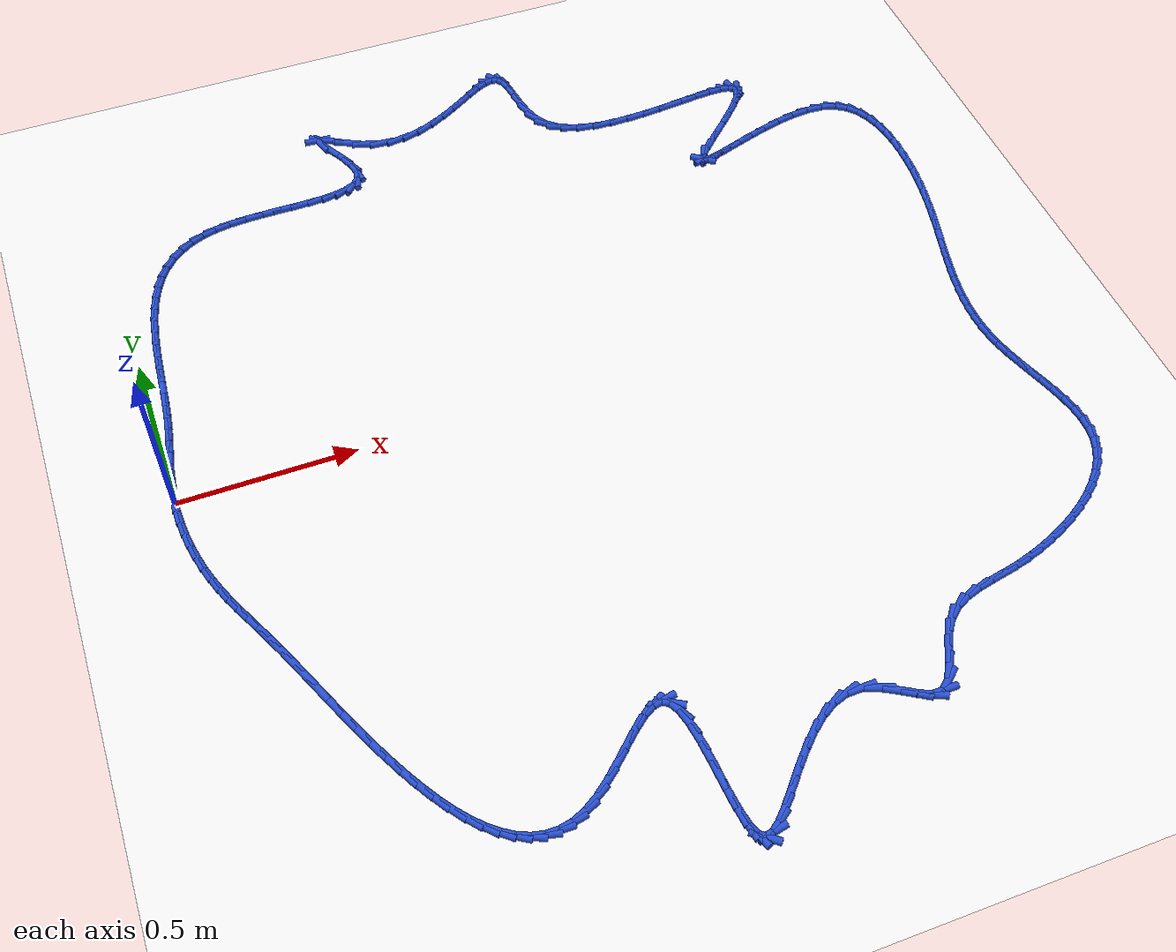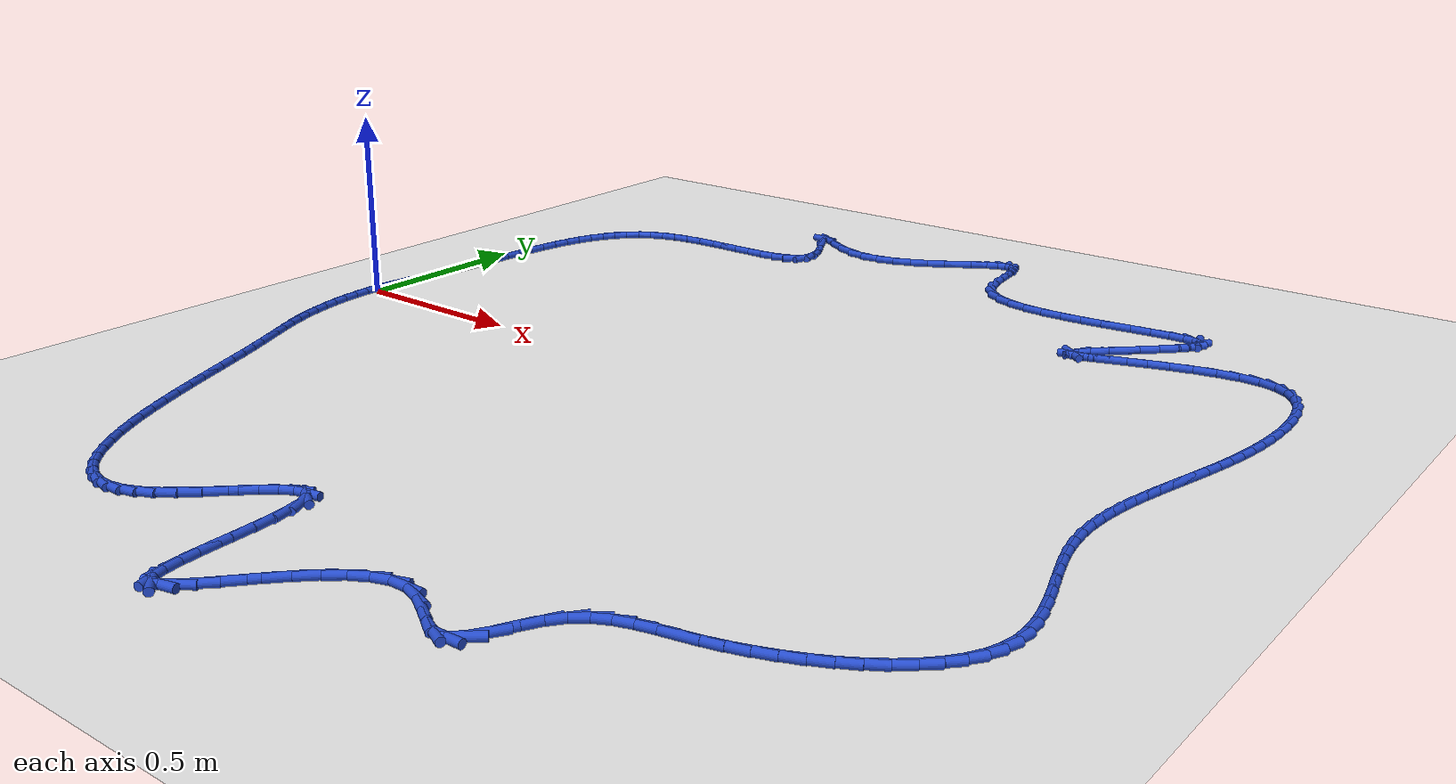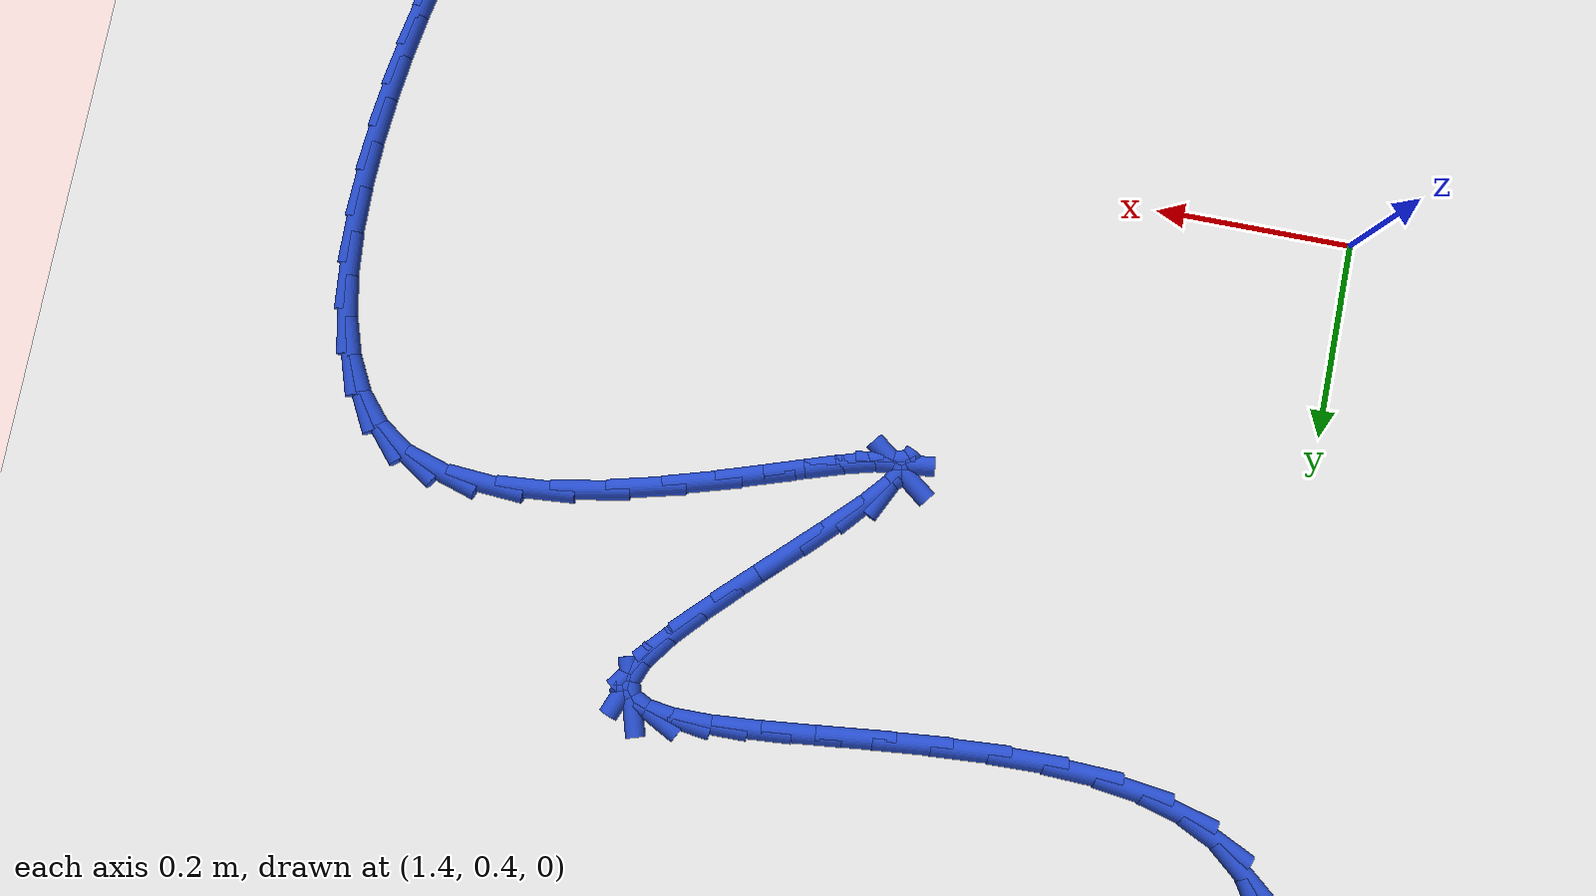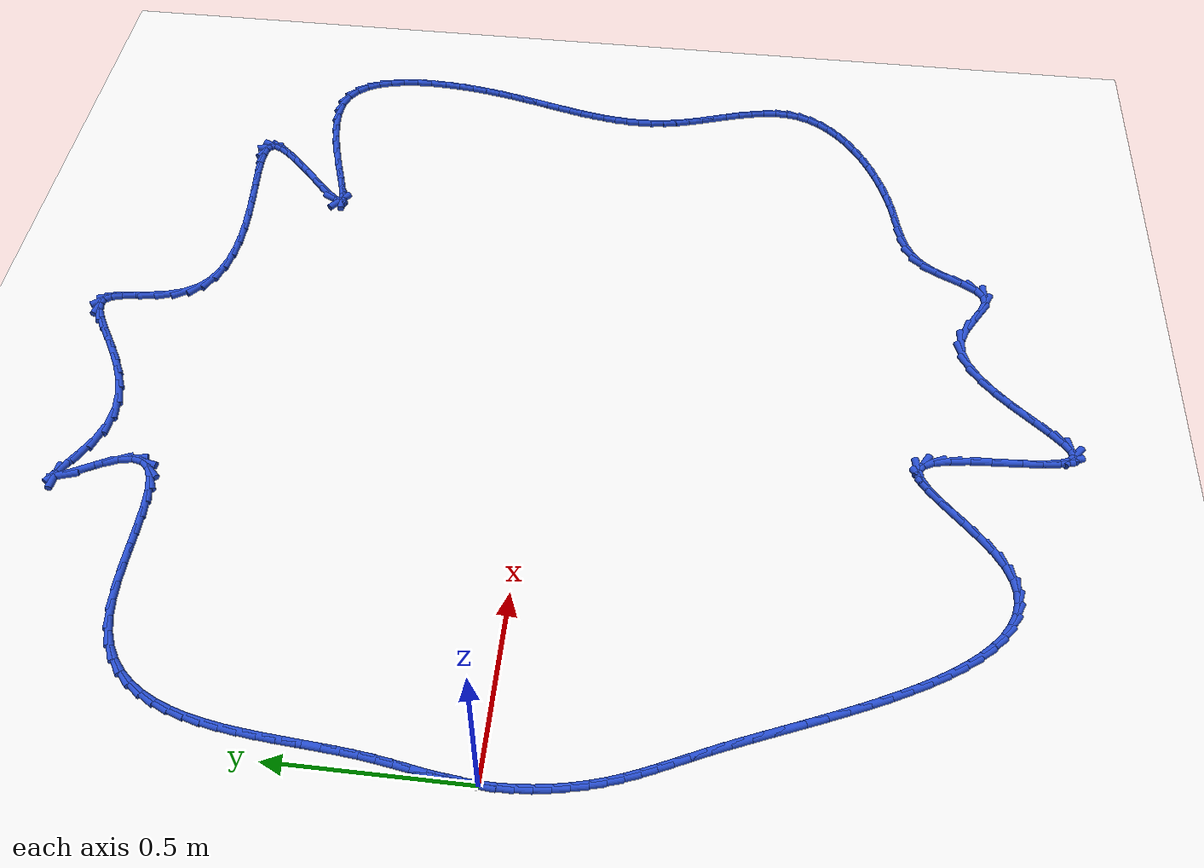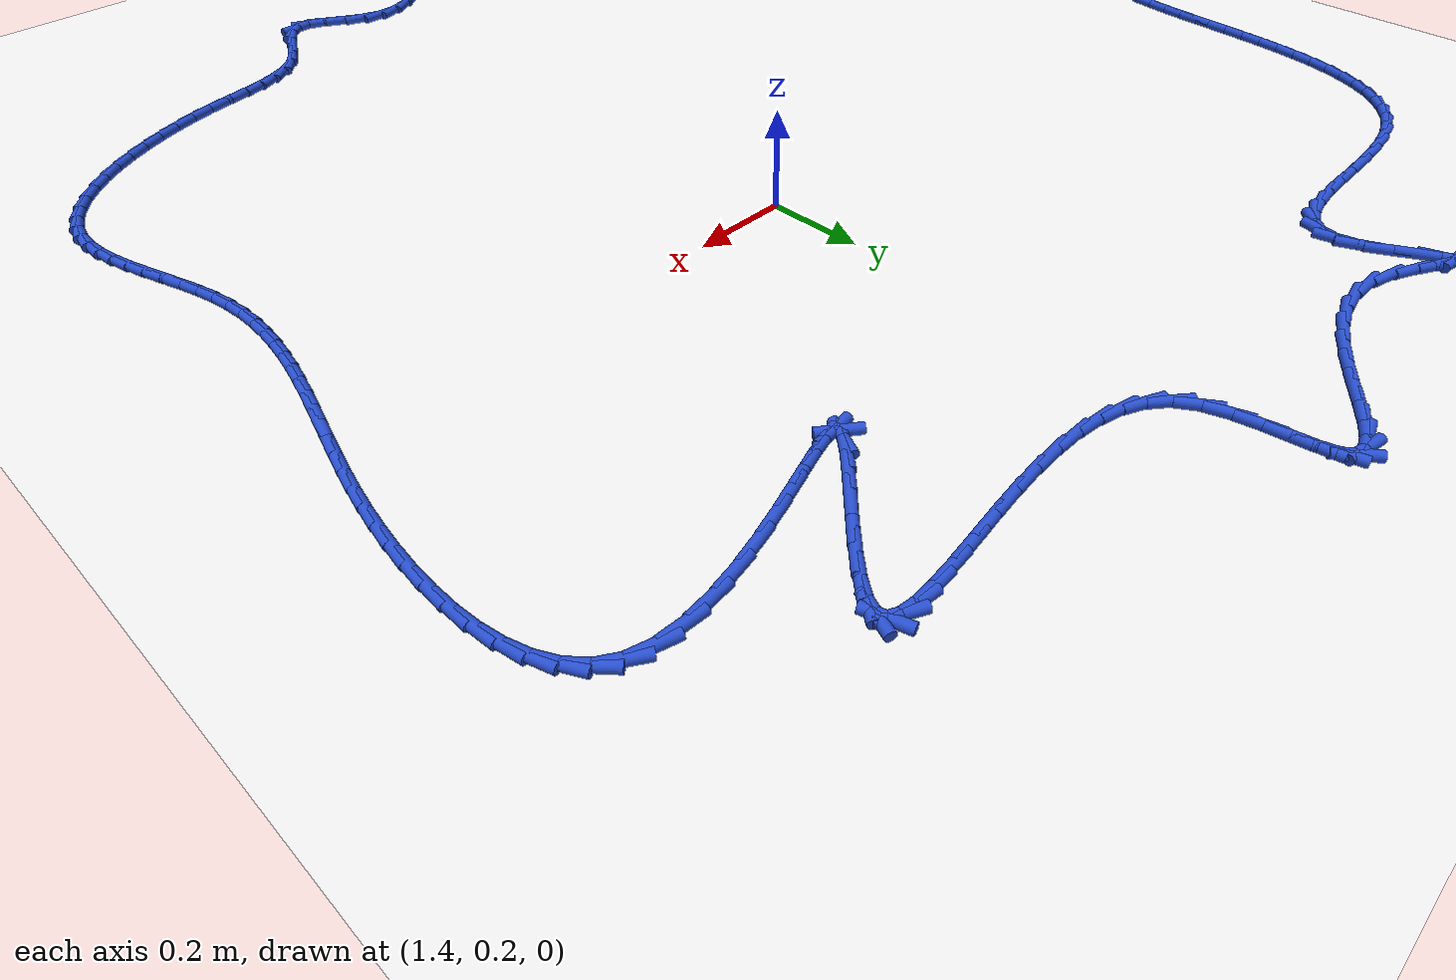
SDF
<sdf version="1.6">
 <world name="default">
  <light name="sun" type="directional">
   <pose>0 0 10 0 -0 0</pose>
   <diffuse>0.8 0.8 0.8 1</diffuse>
   <specular>0.2 0.2 0.2 1</specular>
   <attenuation>
    <range>1000</range>
    <constant>0.9</constant>
    <linear>0.01</linear>
    <quadratic>0.001</quadratic>
   </attenuation>
   <direction>-0.5 0.1 -0.9</direction>
  </light>
  <model name="ground_plane">
   <static>1</static>
   <link name="link">
    <collision name="collision">
     <geometry><plane><normal>0 0 1</normal><size>100 100</size></plane></geometry>
     <surface><friction><ode><mu>100</mu><mu2>50</mu2></ode></friction></surface>
    </collision>
    <visual name="visual">
     <cast_shadows>0</cast_shadows>
     <geometry><plane><normal>0 0 1</normal><size>100 100</size></plane></geometry>
     <material>
      <script><uri>file://media/materials/scripts/gazebo.material</uri><name>Gazebo/WhiteGlow</name></script>
     </material>
    </visual>
   </link>
  </model>
  <gravity>0 0 -9.8</gravity>
  <magnetic_field>6e-06 2.3e-05 -4.2e-05</magnetic_field>
  <atmosphere type="adiabatic"/>
  <physics name="default_physics" default="0" type="ode">
   <max_step_size>0.001</max_step_size>
   <real_time_factor>1</real_time_factor>
   <real_time_update_rate>1000</real_time_update_rate>
  </physics>
  <scene><ambient>0.4 0.4 0.4 1</ambient><background>0.7 0.7 0.7 1</background><shadows>1</shadows></scene>
  <spherical_coordinates>
   <surface_model>EARTH_WGS84</surface_model>
   <latitude_deg>0</latitude_deg>
   <longitude_deg>0</longitude_deg>
   <elevation>0</elevation>
   <heading_deg>0</heading_deg>
  </spherical_coordinates>
  <model name="line">
   <link name="link_0">
    <pose>-6.938893903907228e-18 -6.245004513516506e-17 0.01 0 1.57 1.5021006200074025</pose>
    <collision name="collision">
     <geometry><cylinder><radius>0.01</radius><length>0.08</length></cylinder></geometry>
    </collision>
    <visual name="visual">
     <material>
      <script><name>Gazebo/Blue</name><uri>file://media/materials/scripts/gazebo.material</uri></script>
     </material>
     <geometry><cylinder><radius>0.01</radius><length>0.08</length></cylinder></geometry>
    </visual>
   </link>
   <link name="link_1">
    <pose>0.0027267239276529457 0.03963032738421461 0.01 0 1.57 1.4554943198196943</pose>
    <collision name="collision">
     <geometry><cylinder><radius>0.01</radius><length>0.08</length></cylinder></geometry>
    </collision>
    <visual name="visual">
     <material>
      <script><name>Gazebo/Blue</name><uri>file://media/materials/scripts/gazebo.material</uri></script>
     </material>
     <geometry><cylinder><radius>0.01</radius><length>0.08</length></cylinder></geometry>
    </visual>
   </link>
   <link name="link_2">
    <pose>0.007264452210305063 0.07881092391591504 0.01 0 1.57 1.4231866468837562</pose>
    <collision name="collision">
     <geometry><cylinder><radius>0.01</radius><length>0.08</length></cylinder></geometry>
    </collision>
    <visual name="visual">
     <material>
      <script><name>Gazebo/Blue</name><uri>file://media/materials/scripts/gazebo.material</uri></script>
     </material>
     <geometry><cylinder><radius>0.01</radius><length>0.08</length></cylinder></geometry>
    </visual>
   </link>
   <link name="link_3">
    <pose>0.013079901349454644 0.11792184670235839 0.01 0 1.57 1.4059026485359816</pose>
    <collision name="collision">
     <geometry><cylinder><radius>0.01</radius><length>0.08</length></cylinder></geometry>
    </collision>
    <visual name="visual">
     <material>
      <script><name>Gazebo/Blue</name><uri>file://media/materials/scripts/gazebo.material</uri></script>
     </material>
     <geometry><cylinder><radius>0.01</radius><length>0.08</length></cylinder></geometry>
    </visual>
   </link>
   <link name="link_4">
    <pose>0.01963978784659997 0.1573431528508017 0.01 0 1.57 1.4035683912971355</pose>
    <collision name="collision">
     <geometry><cylinder><radius>0.01</radius><length>0.08</length></cylinder></geometry>
    </collision>
    <visual name="visual">
     <material>
      <script><name>Gazebo/Blue</name><uri>file://media/materials/scripts/gazebo.material</uri></script>
     </material>
     <geometry><cylinder><radius>0.01</radius><length>0.08</length></cylinder></geometry>
    </visual>
   </link>
   <link name="link_5">
    <pose>0.026410828203239364 0.1974548994685022 0.01 0 1.57 1.4154633653897009</pose>
    <collision name="collision">
     <geometry><cylinder><radius>0.01</radius><length>0.08</length></cylinder></geometry>
    </collision>
    <visual name="visual">
     <material>
      <script><name>Gazebo/Blue</name><uri>file://media/materials/scripts/gazebo.material</uri></script>
     </material>
     <geometry><cylinder><radius>0.01</radius><length>0.08</length></cylinder></geometry>
    </visual>
   </link>
   <link name="link_6">
    <pose>0.0328597389208711 0.23863714366271702 0.01 0 1.57 1.4402662695296489</pose>
    <collision name="collision">
     <geometry><cylinder><radius>0.01</radius><length>0.08</length></cylinder></geometry>
    </collision>
    <visual name="visual">
     <material>
      <script><name>Gazebo/Blue</name><uri>file://media/materials/scripts/gazebo.material</uri></script>
     </material>
     <geometry><cylinder><radius>0.01</radius><length>0.08</length></cylinder></geometry>
    </visual>
   </link>
   <link name="link_7">
    <pose>0.038456108458912466 0.2812675512997279 0.01 0 1.57 1.4690482943396301</pose>
    <collision name="collision">
     <geometry><cylinder><radius>0.01</radius><length>0.08</length></cylinder></geometry>
    </collision>
    <visual name="visual">
     <material>
      <script><name>Gazebo/Blue</name><uri>file://media/materials/scripts/gazebo.material</uri></script>
     </material>
     <geometry><cylinder><radius>0.01</radius><length>0.08</length></cylinder></geometry>
    </visual>
   </link>
   <link name="link_8">
    <pose>0.0429696073407799 0.32547393481912695 0.01 0 1.57 1.488264325107925</pose>
    <collision name="collision">
     <geometry><cylinder><radius>0.01</radius><length>0.08</length></cylinder></geometry>
    </collision>
    <visual name="visual">
     <material>
      <script><name>Gazebo/Blue</name><uri>file://media/materials/scripts/gazebo.material</uri></script>
     </material>
     <geometry><cylinder><radius>0.01</radius><length>0.08</length></cylinder></geometry>
    </visual>
   </link>
   <link name="link_9">
    <pose>0.04672879912465362 0.3709187628207979 0.01 0 1.57 1.4976051488358824</pose>
    <collision name="collision">
     <geometry><cylinder><radius>0.01</radius><length>0.08</length></cylinder></geometry>
    </collision>
    <visual name="visual">
     <material>
      <script><name>Gazebo/Blue</name><uri>file://media/materials/scripts/gazebo.material</uri></script>
     </material>
     <geometry><cylinder><radius>0.01</radius><length>0.08</length></cylinder></geometry>
    </visual>
   </link>
   <link name="link_10">
    <pose>0.05012324476902144 0.4172137164324141 0.01 0 1.57 1.4977975830449848</pose>
    <collision name="collision">
     <geometry><cylinder><radius>0.01</radius><length>0.08</length></cylinder></geometry>
    </collision>
    <visual name="visual">
     <material>
      <script><name>Gazebo/Blue</name><uri>file://media/materials/scripts/gazebo.material</uri></script>
     </material>
     <geometry><cylinder><radius>0.01</radius><length>0.08</length></cylinder></geometry>
    </visual>
   </link>
   <link name="link_11">
    <pose>0.05354250523237119 0.4639704767816501 0.01 0 1.57 1.489116066419774</pose>
    <collision name="collision">
     <geometry><cylinder><radius>0.01</radius><length>0.08</length></cylinder></geometry>
    </collision>
    <visual name="visual">
     <material>
      <script><name>Gazebo/Blue</name><uri>file://media/materials/scripts/gazebo.material</uri></script>
     </material>
     <geometry><cylinder><radius>0.01</radius><length>0.08</length></cylinder></geometry>
    </visual>
   </link>
   <link name="link_12">
    <pose>0.05737614147319069 0.5108007249961795 0.01 0 1.57 1.4714250133631803</pose>
    <collision name="collision">
     <geometry><cylinder><radius>0.01</radius><length>0.08</length></cylinder></geometry>
    </collision>
    <visual name="visual">
     <material>
      <script><name>Gazebo/Blue</name><uri>file://media/materials/scripts/gazebo.material</uri></script>
     </material>
     <geometry><cylinder><radius>0.01</radius><length>0.08</length></cylinder></geometry>
    </visual>
   </link>
   <link name="link_13">
    <pose>0.06201371444996775 0.5573161422036758 0.01 0 1.57 1.4441952107664746</pose>
    <collision name="collision">
     <geometry><cylinder><radius>0.01</radius><length>0.08</length></cylinder></geometry>
    </collision>
    <visual name="visual">
     <material>
      <script><name>Gazebo/Blue</name><uri>file://media/materials/scripts/gazebo.material</uri></script>
     </material>
     <geometry><cylinder><radius>0.01</radius><length>0.08</length></cylinder></geometry>
    </visual>
   </link>
   <link name="link_14">
    <pose>0.06784478512119022 0.6031284095318131 0.01 0 1.57 1.4065036133232842</pose>
    <collision name="collision">
     <geometry><cylinder><radius>0.01</radius><length>0.08</length></cylinder></geometry>
    </collision>
    <visual name="visual">
     <material>
      <script><name>Gazebo/Blue</name><uri>file://media/materials/scripts/gazebo.material</uri></script>
     </material>
     <geometry><cylinder><radius>0.01</radius><length>0.08</length></cylinder></geometry>
    </visual>
   </link>
   <link name="link_15">
    <pose>0.0752589144453459 0.6478492081082656 0.01 0 1.57 1.3570331334644816</pose>
    <collision name="collision">
     <geometry><cylinder><radius>0.01</radius><length>0.08</length></cylinder></geometry>
    </collision>
    <visual name="visual">
     <material>
      <script><name>Gazebo/Blue</name><uri>file://media/materials/scripts/gazebo.material</uri></script>
     </material>
     <geometry><cylinder><radius>0.01</radius><length>0.08</length></cylinder></geometry>
    </visual>
   </link>
   <link name="link_16">
    <pose>0.08464566338092261 0.6910902190607068 0.01 0 1.57 1.2941041055894604</pose>
    <collision name="collision">
     <geometry><cylinder><radius>0.01</radius><length>0.08</length></cylinder></geometry>
    </collision>
    <visual name="visual">
     <material>
      <script><name>Gazebo/Blue</name><uri>file://media/materials/scripts/gazebo.material</uri></script>
     </material>
     <geometry><cylinder><radius>0.01</radius><length>0.08</length></cylinder></geometry>
    </visual>
   </link>
   <link name="link_17">
    <pose>0.0963945928864082 0.7324631235168105 0.01 0 1.57 1.215796517895862</pose>
    <collision name="collision">
     <geometry><cylinder><radius>0.01</radius><length>0.08</length></cylinder></geometry>
    </collision>
    <visual name="visual">
     <material>
      <script><name>Gazebo/Blue</name><uri>file://media/materials/scripts/gazebo.material</uri></script>
     </material>
     <geometry><cylinder><radius>0.01</radius><length>0.08</length></cylinder></geometry>
    </visual>
   </link>
   <link name="link_18">
    <pose>0.11089526392029046 0.7715796026042507 0.01 0 1.57 1.1202603138324374</pose>
    <collision name="collision">
     <geometry><cylinder><radius>0.01</radius><length>0.08</length></cylinder></geometry>
    </collision>
    <visual name="visual">
     <material>
      <script><name>Gazebo/Blue</name><uri>file://media/materials/scripts/gazebo.material</uri></script>
     </material>
     <geometry><cylinder><radius>0.01</radius><length>0.08</length></cylinder></geometry>
    </visual>
   </link>
   <link name="link_19">
    <pose>0.1285372374410572 0.8080513374507012 0.01 0 1.57 1.0063334147361882</pose>
    <collision name="collision">
     <geometry><cylinder><radius>0.01</radius><length>0.08</length></cylinder></geometry>
    </collision>
    <visual name="visual">
     <material>
      <script><name>Gazebo/Blue</name><uri>file://media/materials/scripts/gazebo.material</uri></script>
     </material>
     <geometry><cylinder><radius>0.01</radius><length>0.08</length></cylinder></geometry>
    </visual>
   </link>
   <link name="link_20">
    <pose>0.1497100744071963 0.8414900091838358 0.01 0 1.57 0.8745097342246216</pose>
    <collision name="collision">
     <geometry><cylinder><radius>0.01</radius><length>0.08</length></cylinder></geometry>
    </collision>
    <visual name="visual">
     <material>
      <script><name>Gazebo/Blue</name><uri>file://media/materials/scripts/gazebo.material</uri></script>
     </material>
     <geometry><cylinder><radius>0.01</radius><length>0.08</length></cylinder></geometry>
    </visual>
   </link>
   <link name="link_21">
    <pose>0.17480333577719556 0.8715072989313284 0.01 0 1.57 0.7279966299282523</pose>
    <collision name="collision">
     <geometry><cylinder><radius>0.01</radius><length>0.08</length></cylinder></geometry>
    </collision>
    <visual name="visual">
     <material>
      <script><name>Gazebo/Blue</name><uri>file://media/materials/scripts/gazebo.material</uri></script>
     </material>
     <geometry><cylinder><radius>0.01</radius><length>0.08</length></cylinder></geometry>
    </visual>
   </link>
   <link name="link_22">
    <pose>0.20420658250954285 0.8977148878208531 0.01 0 1.57 0.5731269458894008</pose>
    <collision name="collision">
     <geometry><cylinder><radius>0.01</radius><length>0.08</length></cylinder></geometry>
    </collision>
    <visual name="visual">
     <material>
      <script><name>Gazebo/Blue</name><uri>file://media/materials/scripts/gazebo.material</uri></script>
     </material>
     <geometry><cylinder><radius>0.01</radius><length>0.08</length></cylinder></geometry>
    </visual>
   </link>
   <link name="link_23">
    <pose>0.23830937556272588 0.9197244569800833 0.01 0 1.57 0.4183225107185028</pose>
    <collision name="collision">
     <geometry><cylinder><radius>0.01</radius><length>0.08</length></cylinder></geometry>
    </collision>
    <visual name="visual">
     <material>
      <script><name>Gazebo/Blue</name><uri>file://media/materials/scripts/gazebo.material</uri></script>
     </material>
     <geometry><cylinder><radius>0.01</radius><length>0.08</length></cylinder></geometry>
    </visual>
   </link>
   <link name="link_24">
    <pose>0.27750127589523255 0.9371476875366931 0.01 0 1.57 0.2717907313782398</pose>
    <collision name="collision">
     <geometry><cylinder><radius>0.01</radius><length>0.08</length></cylinder></geometry>
    </collision>
    <visual name="visual">
     <material>
      <script><name>Gazebo/Blue</name><uri>file://media/materials/scripts/gazebo.material</uri></script>
     </material>
     <geometry><cylinder><radius>0.01</radius><length>0.08</length></cylinder></geometry>
    </visual>
   </link>
   <link name="link_25">
    <pose>0.32217133962764966 0.949596652982366 0.01 0 1.57 0.1483278691495684</pose>
    <collision name="collision">
     <geometry><cylinder><radius>0.01</radius><length>0.08</length></cylinder></geometry>
    </collision>
    <visual name="visual">
     <material>
      <script><name>Gazebo/Blue</name><uri>file://media/materials/scripts/gazebo.material</uri></script>
     </material>
     <geometry><cylinder><radius>0.01</radius><length>0.08</length></cylinder></geometry>
    </visual>
   </link>
   <link name="link_26">
    <pose>0.37220704788992615 0.9570732548593075 0.01 0 1.57 0.0672593623460096</pose>
    <collision name="collision">
     <geometry><cylinder><radius>0.01</radius><length>0.08</length></cylinder></geometry>
    </collision>
    <visual name="visual">
     <material>
      <script><name>Gazebo/Blue</name><uri>file://media/materials/scripts/gazebo.material</uri></script>
     </material>
     <geometry><cylinder><radius>0.01</radius><length>0.08</length></cylinder></geometry>
    </visual>
   </link>
   <link name="link_27">
    <pose>0.42605352509631317 0.960700405759176 0.01 0 1.57 0.019710770947912463</pose>
    <collision name="collision">
     <geometry><cylinder><radius>0.01</radius><length>0.08</length></cylinder></geometry>
    </collision>
    <visual name="visual">
     <material>
      <script><name>Gazebo/Blue</name><uri>file://media/materials/scripts/gazebo.material</uri></script>
     </material>
     <geometry><cylinder><radius>0.01</radius><length>0.08</length></cylinder></geometry>
    </visual>
   </link>
   <link name="link_28">
    <pose>0.48189821436977776 0.9618012902116498 0.01 0 1.57 -0.0018239643694814589</pose>
    <collision name="collision">
     <geometry><cylinder><radius>0.01</radius><length>0.08</length></cylinder></geometry>
    </collision>
    <visual name="visual">
     <material>
      <script><name>Gazebo/Blue</name><uri>file://media/materials/scripts/gazebo.material</uri></script>
     </material>
     <geometry><cylinder><radius>0.01</radius><length>0.08</length></cylinder></geometry>
    </visual>
   </link>
   <link name="link_29">
    <pose>0.5379285588332865 0.9616990927464069 0.01 0 1.57 0.0003291178858828716</pose>
    <collision name="collision">
     <geometry><cylinder><radius>0.01</radius><length>0.08</length></cylinder></geometry>
    </collision>
    <visual name="visual">
     <material>
      <script><name>Gazebo/Blue</name><uri>file://media/materials/scripts/gazebo.material</uri></script>
     </material>
     <geometry><cylinder><radius>0.01</radius><length>0.08</length></cylinder></geometry>
    </visual>
   </link>
   <link name="link_30">
    <pose>0.5923320016098067 0.9617169978931247 0.01 0 1.57 0.028663224170669157</pose>
    <collision name="collision">
     <geometry><cylinder><radius>0.01</radius><length>0.08</length></cylinder></geometry>
    </collision>
    <visual name="visual">
     <material>
      <script><name>Gazebo/Blue</name><uri>file://media/materials/scripts/gazebo.material</uri></script>
     </material>
     <geometry><cylinder><radius>0.01</radius><length>0.08</length></cylinder></geometry>
    </visual>
   </link>
   <link name="link_31">
    <pose>0.6432959858223048 0.963178190181482 0.01 0 1.57 0.09222249360228521</pose>
    <collision name="collision">
     <geometry><cylinder><radius>0.01</radius><length>0.08</length></cylinder></geometry>
    </collision>
    <visual name="visual">
     <material>
      <script><name>Gazebo/Blue</name><uri>file://media/materials/scripts/gazebo.material</uri></script>
     </material>
     <geometry><cylinder><radius>0.01</radius><length>0.08</length></cylinder></geometry>
    </visual>
   </link>
   <link name="link_32">
    <pose>0.6890079545937482 0.9674058541411569 0.01 0 1.57 0.21197721846874035</pose>
    <collision name="collision">
     <geometry><cylinder><radius>0.01</radius><length>0.08</length></cylinder></geometry>
    </collision>
    <visual name="visual">
     <material>
      <script><name>Gazebo/Blue</name><uri>file://media/materials/scripts/gazebo.material</uri></script>
     </material>
     <geometry><cylinder><radius>0.01</radius><length>0.08</length></cylinder></geometry>
    </visual>
   </link>
   <link name="link_33">
    <pose>0.7276553510471031 0.9757231743018265 0.01 0 1.57 0.4321318627183691</pose>
    <collision name="collision">
     <geometry><cylinder><radius>0.01</radius><length>0.08</length></cylinder></geometry>
    </collision>
    <visual name="visual">
     <material>
      <script><name>Gazebo/Blue</name><uri>file://media/materials/scripts/gazebo.material</uri></script>
     </material>
     <geometry><cylinder><radius>0.01</radius><length>0.08</length></cylinder></geometry>
    </visual>
   </link>
   <link name="link_34">
    <pose>0.757425618305337 0.98945333519317 0.01 0 1.57 0.8204209601151605</pose>
    <collision name="collision">
     <geometry><cylinder><radius>0.01</radius><length>0.08</length></cylinder></geometry>
    </collision>
    <visual name="visual">
     <material>
      <script><name>Gazebo/Blue</name><uri>file://media/materials/scripts/gazebo.material</uri></script>
     </material>
     <geometry><cylinder><radius>0.01</radius><length>0.08</length></cylinder></geometry>
    </visual>
   </link>
   <link name="link_35">
    <pose>0.7765061994914164 1.009919521344865 0.01 0 1.57 1.3441454457149902</pose>
    <collision name="collision">
     <geometry><cylinder><radius>0.01</radius><length>0.08</length></cylinder></geometry>
    </collision>
    <visual name="visual">
     <material>
      <script><name>Gazebo/Blue</name><uri>file://media/materials/scripts/gazebo.material</uri></script>
     </material>
     <geometry><cylinder><radius>0.01</radius><length>0.08</length></cylinder></geometry>
    </visual>
   </link>
   <link name="link_36">
    <pose>0.7830845377283083 1.0384449172865893 0.01 0 1.57 -1.3707157688812357</pose>
    <collision name="collision">
     <geometry><cylinder><radius>0.01</radius><length>0.08</length></cylinder></geometry>
    </collision>
    <visual name="visual">
     <material>
      <script><name>Gazebo/Blue</name><uri>file://media/materials/scripts/gazebo.material</uri></script>
     </material>
     <geometry><cylinder><radius>0.01</radius><length>0.08</length></cylinder></geometry>
    </visual>
   </link>
   <link name="link_37">
    <pose>0.7754078762697585 1.0762994152191472 0.01 0 1.57 -1.1551632312955453</pose>
    <collision name="collision">
     <geometry><cylinder><radius>0.01</radius><length>0.08</length></cylinder></geometry>
    </collision>
    <visual name="visual">
     <material>
      <script><name>Gazebo/Blue</name><uri>file://media/materials/scripts/gazebo.material</uri></script>
     </material>
     <geometry><cylinder><radius>0.01</radius><length>0.08</length></cylinder></geometry>
    </visual>
   </link>
   <link name="link_38">
    <pose>0.7555140840587454 1.1213747998336012 0.01 0 1.57 -1.0780575640294277</pose>
    <collision name="collision">
     <geometry><cylinder><radius>0.01</radius><length>0.08</length></cylinder></geometry>
    </collision>
    <visual name="visual">
     <material>
      <script><name>Gazebo/Blue</name><uri>file://media/materials/scripts/gazebo.material</uri></script>
     </material>
     <geometry><cylinder><radius>0.01</radius><length>0.08</length></cylinder></geometry>
    </visual>
   </link>
   <link name="link_39">
    <pose>0.7314360648644153 1.1662202359403488 0.01 0 1.57 -1.0780818511939423</pose>
    <collision name="collision">
     <geometry><cylinder><radius>0.01</radius><length>0.08</length></cylinder></geometry>
    </collision>
    <visual name="visual">
     <material>
      <script><name>Gazebo/Blue</name><uri>file://media/materials/scripts/gazebo.material</uri></script>
     </material>
     <geometry><cylinder><radius>0.01</radius><length>0.08</length></cylinder></geometry>
    </visual>
   </link>
   <link name="link_40">
    <pose>0.7117366564558378 1.2029126248841853 0.01 0 1.57 -1.2540359668885221</pose>
    <collision name="collision">
     <geometry><cylinder><radius>0.01</radius><length>0.08</length></cylinder></geometry>
    </collision>
    <visual name="visual">
     <material>
      <script><name>Gazebo/Blue</name><uri>file://media/materials/scripts/gazebo.material</uri></script>
     </material>
     <geometry><cylinder><radius>0.01</radius><length>0.08</length></cylinder></geometry>
    </visual>
   </link>
   <link name="link_41">
    <pose>0.7049786966020819 1.223528868009904 0.01 0 1.57 -0.08681060316070477</pose>
    <collision name="collision">
     <geometry><cylinder><radius>0.01</radius><length>0.08</length></cylinder></geometry>
    </collision>
    <visual name="visual">
     <material>
      <script><name>Gazebo/Blue</name><uri>file://media/materials/scripts/gazebo.material</uri></script>
     </material>
     <geometry><cylinder><radius>0.01</radius><length>0.08</length></cylinder></geometry>
    </visual>
   </link>
   <link name="link_42">
    <pose>0.7178736517803205 1.222406628660325 0.01 0 1.57 -0.5250563731306367</pose>
    <collision name="collision">
     <geometry><cylinder><radius>0.01</radius><length>0.08</length></cylinder></geometry>
    </collision>
    <visual name="visual">
     <material>
      <script><name>Gazebo/Blue</name><uri>file://media/materials/scripts/gazebo.material</uri></script>
     </material>
     <geometry><cylinder><radius>0.01</radius><length>0.08</length></cylinder></geometry>
    </visual>
   </link>
   <link name="link_43">
    <pose>0.7481270530720846 1.2048809733400576 0.01 0 1.57 -0.5353121489579198</pose>
    <collision name="collision">
     <geometry><cylinder><radius>0.01</radius><length>0.08</length></cylinder></geometry>
    </collision>
    <visual name="visual">
     <material>
      <script><name>Gazebo/Blue</name><uri>file://media/materials/scripts/gazebo.material</uri></script>
     </material>
     <geometry><cylinder><radius>0.01</radius><length>0.08</length></cylinder></geometry>
    </visual>
   </link>
   <link name="link_44">
    <pose>0.7907099607079993 1.1796261084720483 0.01 0 1.57 -0.4534554167849261</pose>
    <collision name="collision">
     <geometry><cylinder><radius>0.01</radius><length>0.08</length></cylinder></geometry>
    </collision>
    <visual name="visual">
     <material>
      <script><name>Gazebo/Blue</name><uri>file://media/materials/scripts/gazebo.material</uri></script>
     </material>
     <geometry><cylinder><radius>0.01</radius><length>0.08</length></cylinder></geometry>
    </visual>
   </link>
   <link name="link_45">
    <pose>0.8405928110042233 1.155317002358899 0.01 0 1.57 -0.27809004849964014</pose>
    <collision name="collision">
     <geometry><cylinder><radius>0.01</radius><length>0.08</length></cylinder></geometry>
    </collision>
    <visual name="visual">
     <material>
      <script><name>Gazebo/Blue</name><uri>file://media/materials/scripts/gazebo.material</uri></script>
     </material>
     <geometry><cylinder><radius>0.01</radius><length>0.08</length></cylinder></geometry>
    </visual>
   </link>
   <link name="link_46">
    <pose>0.8928393934876392 1.1404012520815043 0.01 0 1.57 -0.04532109773640246</pose>
    <collision name="collision">
     <geometry><cylinder><radius>0.01</radius><length>0.08</length></cylinder></geometry>
    </collision>
    <visual name="visual">
     <material>
      <script><name>Gazebo/Blue</name><uri>file://media/materials/scripts/gazebo.material</uri></script>
     </material>
     <geometry><cylinder><radius>0.01</radius><length>0.08</length></cylinder></geometry>
    </visual>
   </link>
   <link name="link_47">
    <pose>0.9446798115000589 1.1380501775057201 0.01 0 1.57 0.15765639621176952</pose>
    <collision name="collision">
     <geometry><cylinder><radius>0.01</radius><length>0.08</length></cylinder></geometry>
    </collision>
    <visual name="visual">
     <material>
      <script><name>Gazebo/Blue</name><uri>file://media/materials/scripts/gazebo.material</uri></script>
     </material>
     <geometry><cylinder><radius>0.01</radius><length>0.08</length></cylinder></geometry>
    </visual>
   </link>
   <link name="link_48">
    <pose>0.9955211972302664 1.1461327237340586 0.01 0 1.57 0.3163457013097217</pose>
    <collision name="collision">
     <geometry><cylinder><radius>0.01</radius><length>0.08</length></cylinder></geometry>
    </collision>
    <visual name="visual">
     <material>
      <script><name>Gazebo/Blue</name><uri>file://media/materials/scripts/gazebo.material</uri></script>
     </material>
     <geometry><cylinder><radius>0.01</radius><length>0.08</length></cylinder></geometry>
    </visual>
   </link>
   <link name="link_49">
    <pose>1.0448661791005334 1.1622852450978343 0.01 0 1.57 0.43248521061305295</pose>
    <collision name="collision">
     <geometry><cylinder><radius>0.01</radius><length>0.08</length></cylinder></geometry>
    </collision>
    <visual name="visual">
     <material>
      <script><name>Gazebo/Blue</name><uri>file://media/materials/scripts/gazebo.material</uri></script>
     </material>
     <geometry><cylinder><radius>0.01</radius><length>0.08</length></cylinder></geometry>
    </visual>
   </link>
   <link name="link_50">
    <pose>1.0922173855331319 1.1841440959283611 0.01 0 1.57 0.5118432032365489</pose>
    <collision name="collision">
     <geometry><cylinder><radius>0.01</radius><length>0.08</length></cylinder></geometry>
    </collision>
    <visual name="visual">
     <material>
      <script><name>Gazebo/Blue</name><uri>file://media/materials/scripts/gazebo.material</uri></script>
     </material>
     <geometry><cylinder><radius>0.01</radius><length>0.08</length></cylinder></geometry>
    </visual>
   </link>
   <link name="link_51">
    <pose>1.137077444950333 1.2093456305569525 0.01 0 1.57 0.5587857986424692</pose>
    <collision name="collision">
     <geometry><cylinder><radius>0.01</radius><length>0.08</length></cylinder></geometry>
    </collision>
    <visual name="visual">
     <material>
      <script><name>Gazebo/Blue</name><uri>file://media/materials/scripts/gazebo.material</uri></script>
     </material>
     <geometry><cylinder><radius>0.01</radius><length>0.08</length></cylinder></geometry>
    </visual>
   </link>
   <link name="link_52">
    <pose>1.178948985774408 1.235526203314923 0.01 0 1.57 0.5735367124205788</pose>
    <collision name="collision">
     <geometry><cylinder><radius>0.01</radius><length>0.08</length></cylinder></geometry>
    </collision>
    <visual name="visual">
     <material>
      <script><name>Gazebo/Blue</name><uri>file://media/materials/scripts/gazebo.material</uri></script>
     </material>
     <geometry><cylinder><radius>0.01</radius><length>0.08</length></cylinder></geometry>
    </visual>
   </link>
   <link name="link_53">
    <pose>1.217334636427629 1.260322168533587 0.01 0 1.57 0.5490578116631392</pose>
    <collision name="collision">
     <geometry><cylinder><radius>0.01</radius><length>0.08</length></cylinder></geometry>
    </collision>
    <visual name="visual">
     <material>
      <script><name>Gazebo/Blue</name><uri>file://media/materials/scripts/gazebo.material</uri></script>
     </material>
     <geometry><cylinder><radius>0.01</radius><length>0.08</length></cylinder></geometry>
    </visual>
   </link>
   <link name="link_54">
    <pose>1.251737025332267 1.2813698805442577 0.01 0 1.57 0.4629772458581888</pose>
    <collision name="collision">
     <geometry><cylinder><radius>0.01</radius><length>0.08</length></cylinder></geometry>
    </collision>
    <visual name="visual">
     <material>
      <script><name>Gazebo/Blue</name><uri>file://media/materials/scripts/gazebo.material</uri></script>
     </material>
     <geometry><cylinder><radius>0.01</radius><length>0.08</length></cylinder></geometry>
    </visual>
   </link>
   <link name="link_55">
    <pose>1.2816587809105937 1.2963056936782493 0.01 0 1.57 0.25342503249699866</pose>
    <collision name="collision">
     <geometry><cylinder><radius>0.01</radius><length>0.08</length></cylinder></geometry>
    </collision>
    <visual name="visual">
     <material>
      <script><name>Gazebo/Blue</name><uri>file://media/materials/scripts/gazebo.material</uri></script>
     </material>
     <geometry><cylinder><radius>0.01</radius><length>0.08</length></cylinder></geometry>
    </visual>
   </link>
   <link name="link_56">
    <pose>1.3066025315848806 1.3027659622668761 0.01 0 1.57 -0.22124293583382962</pose>
    <collision name="collision">
     <geometry><cylinder><radius>0.01</radius><length>0.08</length></cylinder></geometry>
    </collision>
    <visual name="visual">
     <material>
      <script><name>Gazebo/Blue</name><uri>file://media/materials/scripts/gazebo.material</uri></script>
     </material>
     <geometry><cylinder><radius>0.01</radius><length>0.08</length></cylinder></geometry>
    </visual>
   </link>
   <link name="link_57">
    <pose>1.3260709057773998 1.2983870406414524 0.01 0 1.57 -0.9132822585294198</pose>
    <collision name="collision">
     <geometry><cylinder><radius>0.01</radius><length>0.08</length></cylinder></geometry>
    </collision>
    <visual name="visual">
     <material>
      <script><name>Gazebo/Blue</name><uri>file://media/materials/scripts/gazebo.material</uri></script>
     </material>
     <geometry><cylinder><radius>0.01</radius><length>0.08</length></cylinder></geometry>
    </visual>
   </link>
   <link name="link_58">
    <pose>1.3395981316970167 1.28086766086414 0.01 0 1.57 -1.3000108692132306</pose>
    <collision name="collision">
     <geometry><cylinder><radius>0.01</radius><length>0.08</length></cylinder></geometry>
    </collision>
    <visual name="visual">
     <material>
      <script><name>Gazebo/Blue</name><uri>file://media/materials/scripts/gazebo.material</uri></script>
     </material>
     <geometry><cylinder><radius>0.01</radius><length>0.08</length></cylinder></geometry>
    </visual>
   </link>
   <link name="link_59">
    <pose>1.3480297054629333 1.2504949875656362 0.01 0 1.57 -1.4215956481731047</pose>
    <collision name="collision">
     <geometry><cylinder><radius>0.01</radius><length>0.08</length></cylinder></geometry>
    </collision>
    <visual name="visual">
     <material>
      <script><name>Gazebo/Blue</name><uri>file://media/materials/scripts/gazebo.material</uri></script>
     </material>
     <geometry><cylinder><radius>0.01</radius><length>0.08</length></cylinder></geometry>
    </visual>
   </link>
   <link name="link_60">
    <pose>1.3539640345998423 1.2110164187400687 0.01 0 1.57 -1.4335843074351822</pose>
    <collision name="collision">
     <geometry><cylinder><radius>0.01</radius><length>0.08</length></cylinder></geometry>
    </collision>
    <visual name="visual">
     <material>
      <script><name>Gazebo/Blue</name><uri>file://media/materials/scripts/gazebo.material</uri></script>
     </material>
     <geometry><cylinder><radius>0.01</radius><length>0.08</length></cylinder></geometry>
    </visual>
   </link>
   <link name="link_61">
    <pose>1.3601217949131053 1.1664207090084457 0.01 0 1.57 -1.374304171634273</pose>
    <collision name="collision">
     <geometry><cylinder><radius>0.01</radius><length>0.08</length></cylinder></geometry>
    </collision>
    <visual name="visual">
     <material>
      <script><name>Gazebo/Blue</name><uri>file://media/materials/scripts/gazebo.material</uri></script>
     </material>
     <geometry><cylinder><radius>0.01</radius><length>0.08</length></cylinder></geometry>
    </visual>
   </link>
   <link name="link_62">
    <pose>1.3692236622080818 1.1206966129917757 0.01 0 1.57 -1.239027662566537</pose>
    <collision name="collision">
     <geometry><cylinder><radius>0.01</radius><length>0.08</length></cylinder></geometry>
    </collision>
    <visual name="visual">
     <material>
      <script><name>Gazebo/Blue</name><uri>file://media/materials/scripts/gazebo.material</uri></script>
     </material>
     <geometry><cylinder><radius>0.01</radius><length>0.08</length></cylinder></geometry>
    </visual>
   </link>
   <link name="link_63">
    <pose>1.3839903122901314 1.0778328853110644 0.01 0 1.57 -1.0006229405166875</pose>
    <collision name="collision">
     <geometry><cylinder><radius>0.01</radius><length>0.08</length></cylinder></geometry>
    </collision>
    <visual name="visual">
     <material>
      <script><name>Gazebo/Blue</name><uri>file://media/materials/scripts/gazebo.material</uri></script>
     </material>
     <geometry><cylinder><radius>0.01</radius><length>0.08</length></cylinder></geometry>
    </visual>
   </link>
   <link name="link_64">
    <pose>1.4071089162337873 1.0417784123709457 0.01 0 1.57 -0.6981134285419979</pose>
    <collision name="collision">
     <geometry><cylinder><radius>0.01</radius><length>0.08</length></cylinder></geometry>
    </collision>
    <visual name="visual">
     <material>
      <script><name>Gazebo/Blue</name><uri>file://media/materials/scripts/gazebo.material</uri></script>
     </material>
     <geometry><cylinder><radius>0.01</radius><length>0.08</length></cylinder></geometry>
    </visual>
   </link>
   <link name="link_65">
    <pose>1.439608513915992 1.01450902388425 0.01 0 1.57 -0.4454312048280866</pose>
    <collision name="collision">
     <geometry><cylinder><radius>0.01</radius><length>0.08</length></cylinder></geometry>
    </collision>
    <visual name="visual">
     <material>
      <script><name>Gazebo/Blue</name><uri>file://media/materials/scripts/gazebo.material</uri></script>
     </material>
     <geometry><cylinder><radius>0.01</radius><length>0.08</length></cylinder></geometry>
    </visual>
   </link>
   <link name="link_66">
    <pose>1.4801323502916675 0.9951616254527385 0.01 0 1.57 -0.26008139689269083</pose>
    <collision name="collision">
     <geometry><cylinder><radius>0.01</radius><length>0.08</length></cylinder></geometry>
    </collision>
    <visual name="visual">
     <material>
      <script><name>Gazebo/Blue</name><uri>file://media/materials/scripts/gazebo.material</uri></script>
     </material>
     <geometry><cylinder><radius>0.01</radius><length>0.08</length></cylinder></geometry>
    </visual>
   </link>
   <link name="link_67">
    <pose>1.5271385664036612 0.9826528623556339 0.01 0 1.57 -0.12928270286523671</pose>
    <collision name="collision">
     <geometry><cylinder><radius>0.01</radius><length>0.08</length></cylinder></geometry>
    </collision>
    <visual name="visual">
     <material>
      <script><name>Gazebo/Blue</name><uri>file://media/materials/scripts/gazebo.material</uri></script>
     </material>
     <geometry><cylinder><radius>0.01</radius><length>0.08</length></cylinder></geometry>
    </visual>
   </link>
   <link name="link_68">
    <pose>1.5790853032948247 0.9758993798721592 0.01 0 1.57 -0.03759257307025724</pose>
    <collision name="collision">
     <geometry><cylinder><radius>0.01</radius><length>0.08</length></cylinder></geometry>
    </collision>
    <visual name="visual">
     <material>
      <script><name>Gazebo/Blue</name><uri>file://media/materials/scripts/gazebo.material</uri></script>
     </material>
     <geometry><cylinder><radius>0.01</radius><length>0.08</length></cylinder></geometry>
    </visual>
   </link>
   <link name="link_69">
    <pose>1.6344307020080053 0.9738178232815377 0.01 0 1.57 0.026339302023560128</pose>
    <collision name="collision">
     <geometry><cylinder><radius>0.01</radius><length>0.08</length></cylinder></geometry>
    </collision>
    <visual name="visual">
     <material>
      <script><name>Gazebo/Blue</name><uri>file://media/materials/scripts/gazebo.material</uri></script>
     </material>
     <geometry><cylinder><radius>0.01</radius><length>0.08</length></cylinder></geometry>
    </visual>
   </link>
   <link name="link_70">
    <pose>1.691632903586054 0.9753248378629921 0.01 0 1.57 0.06964431246586442</pose>
    <collision name="collision">
     <geometry><cylinder><radius>0.01</radius><length>0.08</length></cylinder></geometry>
    </collision>
    <visual name="visual">
     <material>
      <script><name>Gazebo/Blue</name><uri>file://media/materials/scripts/gazebo.material</uri></script>
     </material>
     <geometry><cylinder><radius>0.01</radius><length>0.08</length></cylinder></geometry>
    </visual>
   </link>
   <link name="link_71">
    <pose>1.7491500490718197 0.9793370688957459 0.01 0 1.57 0.09623882612468158</pose>
    <collision name="collision">
     <geometry><cylinder><radius>0.01</radius><length>0.08</length></cylinder></geometry>
    </collision>
    <visual name="visual">
     <material>
      <script><name>Gazebo/Blue</name><uri>file://media/materials/scripts/gazebo.material</uri></script>
     </material>
     <geometry><cylinder><radius>0.01</radius><length>0.08</length></cylinder></geometry>
    </visual>
   </link>
   <link name="link_72">
    <pose>1.8054402795081512 0.9847711616590212 0.01 0 1.57 0.10744047579158085</pose>
    <collision name="collision">
     <geometry><cylinder><radius>0.01</radius><length>0.08</length></cylinder></geometry>
    </collision>
    <visual name="visual">
     <material>
      <script><name>Gazebo/Blue</name><uri>file://media/materials/scripts/gazebo.material</uri></script>
     </material>
     <geometry><cylinder><radius>0.01</radius><length>0.08</length></cylinder></geometry>
    </visual>
   </link>
   <link name="link_73">
    <pose>1.8589617359378987 0.9905437614320417 0.01 0 1.57 0.1018143340458194</pose>
    <collision name="collision">
     <geometry><cylinder><radius>0.01</radius><length>0.08</length></cylinder></geometry>
    </collision>
    <visual name="visual">
     <material>
      <script><name>Gazebo/Blue</name><uri>file://media/materials/scripts/gazebo.material</uri></script>
     </material>
     <geometry><cylinder><radius>0.01</radius><length>0.08</length></cylinder></geometry>
    </visual>
   </link>
   <link name="link_74">
    <pose>1.9081725594039114 0.9955715134940303 0.01 0 1.57 0.07365968134507157</pose>
    <collision name="collision">
     <geometry><cylinder><radius>0.01</radius><length>0.08</length></cylinder></geometry>
    </collision>
    <visual name="visual">
     <material>
      <script><name>Gazebo/Blue</name><uri>file://media/materials/scripts/gazebo.material</uri></script>
     </material>
     <geometry><cylinder><radius>0.01</radius><length>0.08</length></cylinder></geometry>
    </visual>
   </link>
   <link name="link_75">
    <pose>1.951530890949038 0.9987710631242097 0.01 0 1.57 0.008007631987830582</pose>
    <collision name="collision">
     <geometry><cylinder><radius>0.01</radius><length>0.08</length></cylinder></geometry>
    </collision>
    <visual name="visual">
     <material>
      <script><name>Gazebo/Blue</name><uri>file://media/materials/scripts/gazebo.material</uri></script>
     </material>
     <geometry><cylinder><radius>0.01</radius><length>0.08</length></cylinder></geometry>
    </visual>
   </link>
   <link name="link_76">
    <pose>1.9874948716161285 0.9990590556018031 0.01 0 1.57 -0.13630184237400225</pose>
    <collision name="collision">
     <geometry><cylinder><radius>0.01</radius><length>0.08</length></cylinder></geometry>
    </collision>
    <visual name="visual">
     <material>
      <script><name>Gazebo/Blue</name><uri>file://media/materials/scripts/gazebo.material</uri></script>
     </material>
     <geometry><cylinder><radius>0.01</radius><length>0.08</length></cylinder></geometry>
    </visual>
   </link>
   <link name="link_77">
    <pose>2.0145226424480325 0.9953521362060335 0.01 0 1.57 -0.4880114138208025</pose>
    <collision name="collision">
     <geometry><cylinder><radius>0.01</radius><length>0.08</length></cylinder></geometry>
    </collision>
    <visual name="visual">
     <material>
      <script><name>Gazebo/Blue</name><uri>file://media/materials/scripts/gazebo.material</uri></script>
     </material>
     <geometry><cylinder><radius>0.01</radius><length>0.08</length></cylinder></geometry>
    </visual>
   </link>
   <link name="link_78">
    <pose>2.031072344487599 0.9865669502161238 0.01 0 1.57 -1.2765348770322262</pose>
    <collision name="collision">
     <geometry><cylinder><radius>0.01</radius><length>0.08</length></cylinder></geometry>
    </collision>
    <visual name="visual">
     <material>
      <script><name>Gazebo/Blue</name><uri>file://media/materials/scripts/gazebo.material</uri></script>
     </material>
     <geometry><cylinder><radius>0.01</radius><length>0.08</length></cylinder></geometry>
    </visual>
   </link>
   <link name="link_79">
    <pose>2.035602118777677 0.9716201429112967 0.01 0 1.57 1.1871877706583496</pose>
    <collision name="collision">
     <geometry><cylinder><radius>0.01</radius><length>0.08</length></cylinder></geometry>
    </collision>
    <visual name="visual">
     <material>
      <script><name>Gazebo/Blue</name><uri>file://media/materials/scripts/gazebo.material</uri></script>
     </material>
     <geometry><cylinder><radius>0.01</radius><length>0.08</length></cylinder></geometry>
    </visual>
   </link>
   <link name="link_80">
    <pose>2.0266711225792595 0.9494919724691845 0.01 0 1.57 0.9319294835685853</pose>
    <collision name="collision">
     <geometry><cylinder><radius>0.01</radius><length>0.08</length></cylinder></geometry>
    </collision>
    <visual name="visual">
     <material>
      <script><name>Gazebo/Blue</name><uri>file://media/materials/scripts/gazebo.material</uri></script>
     </material>
     <geometry><cylinder><radius>0.01</radius><length>0.08</length></cylinder></geometry>
    </visual>
   </link>
   <link name="link_81">
    <pose>2.005289460436291 0.9207061310167515 0.01 0 1.57 0.8330160934214821</pose>
    <collision name="collision">
     <geometry><cylinder><radius>0.01</radius><length>0.08</length></cylinder></geometry>
    </collision>
    <visual name="visual">
     <material>
      <script><name>Gazebo/Blue</name><uri>file://media/materials/scripts/gazebo.material</uri></script>
     </material>
     <geometry><cylinder><radius>0.01</radius><length>0.08</length></cylinder></geometry>
    </visual>
   </link>
   <link name="link_82">
    <pose>1.974991226310694 0.8873757414217053 0.01 0 1.57 0.7871372419610609</pose>
    <collision name="collision">
     <geometry><cylinder><radius>0.01</radius><length>0.08</length></cylinder></geometry>
    </collision>
    <visual name="visual">
     <material>
      <script><name>Gazebo/Blue</name><uri>file://media/materials/scripts/gazebo.material</uri></script>
     </material>
     <geometry><cylinder><radius>0.01</radius><length>0.08</length></cylinder></geometry>
    </visual>
   </link>
   <link name="link_83">
    <pose>1.939426142758848 0.8516867412954406 0.01 0 1.57 0.7673214474083236</pose>
    <collision name="collision">
     <geometry><cylinder><radius>0.01</radius><length>0.08</length></cylinder></geometry>
    </collision>
    <visual name="visual">
     <material>
      <script><name>Gazebo/Blue</name><uri>file://media/materials/scripts/gazebo.material</uri></script>
     </material>
     <geometry><cylinder><radius>0.01</radius><length>0.08</length></cylinder></geometry>
    </visual>
   </link>
   <link name="link_84">
    <pose>1.9022439323371352 0.8158250682493546 0.01 0 1.57 0.7665417947850478</pose>
    <collision name="collision">
     <geometry><cylinder><radius>0.01</radius><length>0.08</length></cylinder></geometry>
    </collision>
    <visual name="visual">
     <material>
      <script><name>Gazebo/Blue</name><uri>file://media/materials/scripts/gazebo.material</uri></script>
     </material>
     <geometry><cylinder><radius>0.01</radius><length>0.08</length></cylinder></geometry>
    </visual>
   </link>
   <link name="link_85">
    <pose>1.867094317601936 0.7819766598948418 0.01 0 1.57 0.7884752903799574</pose>
    <collision name="collision">
     <geometry><cylinder><radius>0.01</radius><length>0.08</length></cylinder></geometry>
    </collision>
    <visual name="visual">
     <material>
      <script><name>Gazebo/Blue</name><uri>file://media/materials/scripts/gazebo.material</uri></script>
     </material>
     <geometry><cylinder><radius>0.01</radius><length>0.08</length></cylinder></geometry>
    </visual>
   </link>
   <link name="link_86">
    <pose>1.8376270211096326 0.7523274538432992 0.01 0 1.57 0.8573671830383249</pose>
    <collision name="collision">
     <geometry><cylinder><radius>0.01</radius><length>0.08</length></cylinder></geometry>
    </collision>
    <visual name="visual">
     <material>
      <script><name>Gazebo/Blue</name><uri>file://media/materials/scripts/gazebo.material</uri></script>
     </material>
     <geometry><cylinder><radius>0.01</radius><length>0.08</length></cylinder></geometry>
    </visual>
   </link>
   <link name="link_87">
    <pose>1.8174917654166045 0.7290633877061218 0.01 0 1.57 1.1160958172371516</pose>
    <collision name="collision">
     <geometry><cylinder><radius>0.01</radius><length>0.08</length></cylinder></geometry>
    </collision>
    <visual name="visual">
     <material>
      <script><name>Gazebo/Blue</name><uri>file://media/materials/scripts/gazebo.material</uri></script>
     </material>
     <geometry><cylinder><radius>0.01</radius><length>0.08</length></cylinder></geometry>
    </visual>
   </link>
   <link name="link_88">
    <pose>1.8102940030587178 0.7143399917708112 0.01 0 1.57 -0.6568678774520541</pose>
    <collision name="collision">
     <geometry><cylinder><radius>0.01</radius><length>0.08</length></cylinder></geometry>
    </collision>
    <visual name="visual">
     <material>
      <script><name>Gazebo/Blue</name><uri>file://media/materials/scripts/gazebo.material</uri></script>
     </material>
     <geometry><cylinder><radius>0.01</radius><length>0.08</length></cylinder></geometry>
    </visual>
   </link>
   <link name="link_89">
    <pose>1.817458836742531 0.7088152003741723 0.01 0 1.57 0.10959761120638632</pose>
    <collision name="collision">
     <geometry><cylinder><radius>0.01</radius><length>0.08</length></cylinder></geometry>
    </collision>
    <visual name="visual">
     <material>
      <script><name>Gazebo/Blue</name><uri>file://media/materials/scripts/gazebo.material</uri></script>
     </material>
     <geometry><cylinder><radius>0.01</radius><length>0.08</length></cylinder></geometry>
    </visual>
   </link>
   <link name="link_90">
    <pose>1.837280273864114 0.7109963224830775 0.01 0 1.57 0.26325087062807734</pose>
    <collision name="collision">
     <geometry><cylinder><radius>0.01</radius><length>0.08</length></cylinder></geometry>
    </collision>
    <visual name="visual">
     <material>
      <script><name>Gazebo/Blue</name><uri>file://media/materials/scripts/gazebo.material</uri></script>
     </material>
     <geometry><cylinder><radius>0.01</radius><length>0.08</length></cylinder></geometry>
    </visual>
   </link>
   <link name="link_91">
    <pose>1.8678100613052167 0.7192242679112066 0.01 0 1.57 0.3106934483558724</pose>
    <collision name="collision">
     <geometry><cylinder><radius>0.01</radius><length>0.08</length></cylinder></geometry>
    </collision>
    <visual name="visual">
     <material>
      <script><name>Gazebo/Blue</name><uri>file://media/materials/scripts/gazebo.material</uri></script>
     </material>
     <geometry><cylinder><radius>0.01</radius><length>0.08</length></cylinder></geometry>
    </visual>
   </link>
   <link name="link_92">
    <pose>1.907099945947589 0.731839946472239 0.01 0 1.57 0.321303015065137</pose>
    <collision name="collision">
     <geometry><cylinder><radius>0.01</radius><length>0.08</length></cylinder></geometry>
    </collision>
    <visual name="visual">
     <material>
      <script><name>Gazebo/Blue</name><uri>file://media/materials/scripts/gazebo.material</uri></script>
     </material>
     <geometry><cylinder><radius>0.01</radius><length>0.08</length></cylinder></geometry>
    </visual>
   </link>
   <link name="link_93">
    <pose>1.9532016746729786 0.7471842679798536 0.01 0 1.57 0.3115701809112702</pose>
    <collision name="collision">
     <geometry><cylinder><radius>0.01</radius><length>0.08</length></cylinder></geometry>
    </collision>
    <visual name="visual">
     <material>
      <script><name>Gazebo/Blue</name><uri>file://media/materials/scripts/gazebo.material</uri></script>
     </material>
     <geometry><cylinder><radius>0.01</radius><length>0.08</length></cylinder></geometry>
    </visual>
   </link>
   <link name="link_94">
    <pose>2.0041669943631364 0.7635981422477308 0.01 0 1.57 0.2856599593066862</pose>
    <collision name="collision">
     <geometry><cylinder><radius>0.01</radius><length>0.08</length></cylinder></geometry>
    </collision>
    <visual name="visual">
     <material>
      <script><name>Gazebo/Blue</name><uri>file://media/materials/scripts/gazebo.material</uri></script>
     </material>
     <geometry><cylinder><radius>0.01</radius><length>0.08</length></cylinder></geometry>
    </visual>
   </link>
   <link name="link_95">
    <pose>2.0580476518998108 0.7794224790895498 0.01 0 1.57 0.24263968333161215</pose>
    <collision name="collision">
     <geometry><cylinder><radius>0.01</radius><length>0.08</length></cylinder></geometry>
    </collision>
    <visual name="visual">
     <material>
      <script><name>Gazebo/Blue</name><uri>file://media/materials/scripts/gazebo.material</uri></script>
     </material>
     <geometry><cylinder><radius>0.01</radius><length>0.08</length></cylinder></geometry>
    </visual>
   </link>
   <link name="link_96">
    <pose>2.1128953941647524 0.7929981883189902 0.01 0 1.57 0.17758954911010977</pose>
    <collision name="collision">
     <geometry><cylinder><radius>0.01</radius><length>0.08</length></cylinder></geometry>
    </collision>
    <visual name="visual">
     <material>
      <script><name>Gazebo/Blue</name><uri>file://media/materials/scripts/gazebo.material</uri></script>
     </material>
     <geometry><cylinder><radius>0.01</radius><length>0.08</length></cylinder></geometry>
    </visual>
   </link>
   <link name="link_97">
    <pose>2.166761968039709 0.8026661797497314 0.01 0 1.57 0.08034127270707626</pose>
    <collision name="collision">
     <geometry><cylinder><radius>0.01</radius><length>0.08</length></cylinder></geometry>
    </collision>
    <visual name="visual">
     <material>
      <script><name>Gazebo/Blue</name><uri>file://media/materials/scripts/gazebo.material</uri></script>
     </material>
     <geometry><cylinder><radius>0.01</radius><length>0.08</length></cylinder></geometry>
    </visual>
   </link>
   <link name="link_98">
    <pose>2.217699120406431 0.8067673631954532 0.01 0 1.57 -0.06773707305881851</pose>
    <collision name="collision">
     <geometry><cylinder><radius>0.01</radius><length>0.08</length></cylinder></geometry>
    </collision>
    <visual name="visual">
     <material>
      <script><name>Gazebo/Blue</name><uri>file://media/materials/scripts/gazebo.material</uri></script>
     </material>
     <geometry><cylinder><radius>0.01</radius><length>0.08</length></cylinder></geometry>
    </visual>
   </link>
   <link name="link_99">
    <pose>2.2637585981466684 0.8036426484698349 0.01 0 1.57 -0.29581174602810734</pose>
    <collision name="collision">
     <geometry><cylinder><radius>0.01</radius><length>0.08</length></cylinder></geometry>
    </collision>
    <visual name="visual">
     <material>
      <script><name>Gazebo/Blue</name><uri>file://media/materials/scripts/gazebo.material</uri></script>
     </material>
     <geometry><cylinder><radius>0.01</radius><length>0.08</length></cylinder></geometry>
    </visual>
   </link>
   <link name="link_100">
    <pose>2.303029124883706 0.7916748322494609 0.01 0 1.57 -0.586971514379971</pose>
    <collision name="collision">
     <geometry><cylinder><radius>0.01</radius><length>0.08</length></cylinder></geometry>
    </collision>
    <visual name="visual">
     <material>
      <script><name>Gazebo/Blue</name><uri>file://media/materials/scripts/gazebo.material</uri></script>
     </material>
     <geometry><cylinder><radius>0.01</radius><length>0.08</length></cylinder></geometry>
    </visual>
   </link>
   <link name="link_101">
    <pose>2.334763749943402 0.7705656470893085 0.01 0 1.57 -0.8627776583636111</pose>
    <collision name="collision">
     <geometry><cylinder><radius>0.01</radius><length>0.08</length></cylinder></geometry>
    </collision>
    <visual name="visual">
     <material>
      <script><name>Gazebo/Blue</name><uri>file://media/materials/scripts/gazebo.material</uri></script>
     </material>
     <geometry><cylinder><radius>0.01</radius><length>0.08</length></cylinder></geometry>
    </visual>
   </link>
   <link name="link_102">
    <pose>2.3595866222654194 0.7415699927290288 0.01 0 1.57 -1.0883105744944495</pose>
    <collision name="collision">
     <geometry><cylinder><radius>0.01</radius><length>0.08</length></cylinder></geometry>
    </collision>
    <visual name="visual">
     <material>
      <script><name>Gazebo/Blue</name><uri>file://media/materials/scripts/gazebo.material</uri></script>
     </material>
     <geometry><cylinder><radius>0.01</radius><length>0.08</length></cylinder></geometry>
    </visual>
   </link>
   <link name="link_103">
    <pose>2.37820056905022 0.706031894812465 0.01 0 1.57 -1.2594872912058233</pose>
    <collision name="collision">
     <geometry><cylinder><radius>0.01</radius><length>0.08</length></cylinder></geometry>
    </collision>
    <visual name="visual">
     <material>
      <script><name>Gazebo/Blue</name><uri>file://media/materials/scripts/gazebo.material</uri></script>
     </material>
     <geometry><cylinder><radius>0.01</radius><length>0.08</length></cylinder></geometry>
    </visual>
   </link>
   <link name="link_104">
    <pose>2.3913084174982644 0.6652953789834605 0.01 0 1.57 -1.3866665857969944</pose>
    <collision name="collision">
     <geometry><cylinder><radius>0.01</radius><length>0.08</length></cylinder></geometry>
    </collision>
    <visual name="visual">
     <material>
      <script><name>Gazebo/Blue</name><uri>file://media/materials/scripts/gazebo.material</uri></script>
     </material>
     <geometry><cylinder><radius>0.01</radius><length>0.08</length></cylinder></geometry>
    </visual>
   </link>
   <link name="link_105">
    <pose>2.399612994810015 0.6207044708858579 0.01 0 1.57 -1.48177491762271</pose>
    <collision name="collision">
     <geometry><cylinder><radius>0.01</radius><length>0.08</length></cylinder></geometry>
    </collision>
    <visual name="visual">
     <material>
      <script><name>Gazebo/Blue</name><uri>file://media/materials/scripts/gazebo.material</uri></script>
     </material>
     <geometry><cylinder><radius>0.01</radius><length>0.08</length></cylinder></geometry>
    </visual>
   </link>
   <link name="link_106">
    <pose>2.403817128185934 0.5736031961635017 0.01 0 1.57 -1.554088611246273</pose>
    <collision name="collision">
     <geometry><cylinder><radius>0.01</radius><length>0.08</length></cylinder></geometry>
    </collision>
    <visual name="visual">
     <material>
      <script><name>Gazebo/Blue</name><uri>file://media/materials/scripts/gazebo.material</uri></script>
     </material>
     <geometry><cylinder><radius>0.01</radius><length>0.08</length></cylinder></geometry>
    </visual>
   </link>
   <link name="link_107">
    <pose>2.404623644826482 0.5253355804602348 0.01 0 1.57 1.5315510353349273</pose>
    <collision name="collision">
     <geometry><cylinder><radius>0.01</radius><length>0.08</length></cylinder></geometry>
    </collision>
    <visual name="visual">
     <material>
      <script><name>Gazebo/Blue</name><uri>file://media/materials/scripts/gazebo.material</uri></script>
     </material>
     <geometry><cylinder><radius>0.01</radius><length>0.08</length></cylinder></geometry>
    </visual>
   </link>
   <link name="link_108">
    <pose>2.4027353719321223 0.47724564941989955 0.01 0 1.57 1.4866097975274881</pose>
    <collision name="collision">
     <geometry><cylinder><radius>0.01</radius><length>0.08</length></cylinder></geometry>
    </collision>
    <visual name="visual">
     <material>
      <script><name>Gazebo/Blue</name><uri>file://media/materials/scripts/gazebo.material</uri></script>
     </material>
     <geometry><cylinder><radius>0.01</radius><length>0.08</length></cylinder></geometry>
    </visual>
   </link>
   <link name="link_109">
    <pose>2.3987858549141072 0.43044265046446334 0.01 0 1.57 1.4466108797536057</pose>
    <collision name="collision">
     <geometry><cylinder><radius>0.01</radius><length>0.08</length></cylinder></geometry>
    </collision>
    <visual name="visual">
     <material>
      <script><name>Gazebo/Blue</name><uri>file://media/materials/scripts/gazebo.material</uri></script>
     </material>
     <geometry><cylinder><radius>0.01</radius><length>0.08</length></cylinder></geometry>
    </visual>
   </link>
   <link name="link_110">
    <pose>2.393120956566663 0.3850609483798666 0.01 0 1.57 1.4108930804090476</pose>
    <collision name="collision">
     <geometry><cylinder><radius>0.01</radius><length>0.08</length></cylinder></geometry>
    </collision>
    <visual name="visual">
     <material>
      <script><name>Gazebo/Blue</name><uri>file://media/materials/scripts/gazebo.material</uri></script>
     </material>
     <geometry><cylinder><radius>0.01</radius><length>0.08</length></cylinder></geometry>
    </visual>
   </link>
   <link name="link_111">
    <pose>2.386011880425168 0.3409819068641846 0.01 0 1.57 1.3800660663910456</pose>
    <collision name="collision">
     <geometry><cylinder><radius>0.01</radius><length>0.08</length></cylinder></geometry>
    </collision>
    <visual name="visual">
     <material>
      <script><name>Gazebo/Blue</name><uri>file://media/materials/scripts/gazebo.material</uri></script>
     </material>
     <geometry><cylinder><radius>0.01</radius><length>0.08</length></cylinder></geometry>
    </visual>
   </link>
   <link name="link_112">
    <pose>2.377729829885865 0.29808688914399467 0.01 0 1.57 1.3546724113541737</pose>
    <collision name="collision">
     <geometry><cylinder><radius>0.01</radius><length>0.08</length></cylinder></geometry>
    </collision>
    <visual name="visual">
     <material>
      <script><name>Gazebo/Blue</name><uri>file://media/materials/scripts/gazebo.material</uri></script>
     </material>
     <geometry><cylinder><radius>0.01</radius><length>0.08</length></cylinder></geometry>
    </visual>
   </link>
   <link name="link_113">
    <pose>2.368546008344998 0.25625725844587643 0.01 0 1.57 1.3351935770044265</pose>
    <collision name="collision">
     <geometry><cylinder><radius>0.01</radius><length>0.08</length></cylinder></geometry>
    </collision>
    <visual name="visual">
     <material>
      <script><name>Gazebo/Blue</name><uri>file://media/materials/scripts/gazebo.material</uri></script>
     </material>
     <geometry><cylinder><radius>0.01</radius><length>0.08</length></cylinder></geometry>
    </visual>
   </link>
   <link name="link_114">
    <pose>2.358731619198805 0.2153743779964068 0.01 0 1.57 1.3220602082245263</pose>
    <collision name="collision">
     <geometry><cylinder><radius>0.01</radius><length>0.08</length></cylinder></geometry>
    </collision>
    <visual name="visual">
     <material>
      <script><name>Gazebo/Blue</name><uri>file://media/materials/scripts/gazebo.material</uri></script>
     </material>
     <geometry><cylinder><radius>0.01</radius><length>0.08</length></cylinder></geometry>
    </visual>
   </link>
   <link name="link_115">
    <pose>2.3485578658435315 0.17531961102216556 0.01 0 1.57 1.3156633051531208</pose>
    <collision name="collision">
     <geometry><cylinder><radius>0.01</radius><length>0.08</length></cylinder></geometry>
    </collision>
    <visual name="visual">
     <material>
      <script><name>Gazebo/Blue</name><uri>file://media/materials/scripts/gazebo.material</uri></script>
     </material>
     <geometry><cylinder><radius>0.01</radius><length>0.08</length></cylinder></geometry>
    </visual>
   </link>
   <link name="link_116">
    <pose>2.33829595167542 0.13597432074973026 0.01 0 1.57 1.3163626610373997</pose>
    <collision name="collision">
     <geometry><cylinder><radius>0.01</radius><length>0.08</length></cylinder></geometry>
    </collision>
    <visual name="visual">
     <material>
      <script><name>Gazebo/Blue</name><uri>file://media/materials/scripts/gazebo.material</uri></script>
     </material>
     <geometry><cylinder><radius>0.01</radius><length>0.08</length></cylinder></geometry>
    </visual>
   </link>
   <link name="link_117">
    <pose>2.3282170800907114 0.09721987040567842 0.01 0 1.57 1.3244889367777382</pose>
    <collision name="collision">
     <geometry><cylinder><radius>0.01</radius><length>0.08</length></cylinder></geometry>
    </collision>
    <visual name="visual">
     <material>
      <script><name>Gazebo/Blue</name><uri>file://media/materials/scripts/gazebo.material</uri></script>
     </material>
     <geometry><cylinder><radius>0.01</radius><length>0.08</length></cylinder></geometry>
    </visual>
   </link>
   <link name="link_118">
    <pose>2.318592454485649 0.05893762321659033 0.01 0 1.57 1.3403357847958324</pose>
    <collision name="collision">
     <geometry><cylinder><radius>0.01</radius><length>0.08</length></cylinder></geometry>
    </collision>
    <visual name="visual">
     <material>
      <script><name>Gazebo/Blue</name><uri>file://media/materials/scripts/gazebo.material</uri></script>
     </material>
     <geometry><cylinder><radius>0.01</radius><length>0.08</length></cylinder></geometry>
    </visual>
   </link>
   <link name="link_119">
    <pose>2.309693278256476 0.021008942409043392 0.01 0 1.57 1.36413864837577</pose>
    <collision name="collision">
     <geometry><cylinder><radius>0.01</radius><length>0.08</length></cylinder></geometry>
    </collision>
    <visual name="visual">
     <material>
      <script><name>Gazebo/Blue</name><uri>file://media/materials/scripts/gazebo.material</uri></script>
     </material>
     <geometry><cylinder><radius>0.01</radius><length>0.08</length></cylinder></geometry>
    </visual>
   </link>
   <link name="link_120">
    <pose>2.3017907547994327 -0.016684808790384094 0.01 0 1.57 1.3960376437807251</pose>
    <collision name="collision">
     <geometry><cylinder><radius>0.01</radius><length>0.08</length></cylinder></geometry>
    </collision>
    <visual name="visual">
     <material>
      <script><name>Gazebo/Blue</name><uri>file://media/materials/scripts/gazebo.material</uri></script>
     </material>
     <geometry><cylinder><radius>0.01</radius><length>0.08</length></cylinder></geometry>
    </visual>
   </link>
   <link name="link_121">
    <pose>2.2951560875107626 -0.05426226715511366 0.01 0 1.57 1.436023962901516</pose>
    <collision name="collision">
     <geometry><cylinder><radius>0.01</radius><length>0.08</length></cylinder></geometry>
    </collision>
    <visual name="visual">
     <material>
      <script><name>Gazebo/Blue</name><uri>file://media/materials/scripts/gazebo.material</uri></script>
     </material>
     <geometry><cylinder><radius>0.01</radius><length>0.08</length></cylinder></geometry>
    </visual>
   </link>
   <link name="link_122">
    <pose>2.2900604797867077 -0.09184206945856803 0.01 0 1.57 1.4838732958816472</pose>
    <collision name="collision">
     <geometry><cylinder><radius>0.01</radius><length>0.08</length></cylinder></geometry>
    </collision>
    <visual name="visual">
     <material>
      <script><name>Gazebo/Blue</name><uri>file://media/materials/scripts/gazebo.material</uri></script>
     </material>
     <geometry><cylinder><radius>0.01</radius><length>0.08</length></cylinder></geometry>
    </visual>
   </link>
   <link name="link_123">
    <pose>2.286775135023512 -0.12954285247416691 0.01 0 1.57 1.5390761921742087</pose>
    <collision name="collision">
     <geometry><cylinder><radius>0.01</radius><length>0.08</length></cylinder></geometry>
    </collision>
    <visual name="visual">
     <material>
      <script><name>Gazebo/Blue</name><uri>file://media/materials/scripts/gazebo.material</uri></script>
     </material>
     <geometry><cylinder><radius>0.01</radius><length>0.08</length></cylinder></geometry>
    </visual>
   </link>
   <link name="link_124">
    <pose>2.285571256617415 -0.16748325297533279 0.01 0 1.57 -1.5408097122815188</pose>
    <collision name="collision">
     <geometry><cylinder><radius>0.01</radius><length>0.08</length></cylinder></geometry>
    </collision>
    <visual name="visual">
     <material>
      <script><name>Gazebo/Blue</name><uri>file://media/materials/scripts/gazebo.material</uri></script>
     </material>
     <geometry><cylinder><radius>0.01</radius><length>0.08</length></cylinder></geometry>
    </visual>
   </link>
   <link name="link_125">
    <pose>2.286720047964662 -0.20578190773548746 0.01 0 1.57 -1.4738066601923003</pose>
    <collision name="collision">
     <geometry><cylinder><radius>0.01</radius><length>0.08</length></cylinder></geometry>
    </collision>
    <visual name="visual">
     <material>
      <script><name>Gazebo/Blue</name><uri>file://media/materials/scripts/gazebo.material</uri></script>
     </material>
     <geometry><cylinder><radius>0.01</radius><length>0.08</length></cylinder></geometry>
    </visual>
   </link>
   <link name="link_126">
    <pose>2.290492712461493 -0.24455745352805344 0.01 0 1.57 -1.4030318139515574</pose>
    <collision name="collision">
     <geometry><cylinder><radius>0.01</radius><length>0.08</length></cylinder></geometry>
    </collision>
    <visual name="visual">
     <material>
      <script><name>Gazebo/Blue</name><uri>file://media/materials/scripts/gazebo.material</uri></script>
     </material>
     <geometry><cylinder><radius>0.01</radius><length>0.08</length></cylinder></geometry>
    </visual>
   </link>
   <link name="link_127">
    <pose>2.2971604535041523 -0.2839285271264505 0.01 0 1.57 -1.3344815896386475</pose>
    <collision name="collision">
     <geometry><cylinder><radius>0.01</radius><length>0.08</length></cylinder></geometry>
    </collision>
    <visual name="visual">
     <material>
      <script><name>Gazebo/Blue</name><uri>file://media/materials/scripts/gazebo.material</uri></script>
     </material>
     <geometry><cylinder><radius>0.01</radius><length>0.08</length></cylinder></geometry>
    </visual>
   </link>
   <link name="link_128">
    <pose>2.3068004881981934 -0.3239595256845751 0.01 0 1.57 -1.2864131666909573</pose>
    <collision name="collision">
     <geometry><cylinder><radius>0.01</radius><length>0.08</length></cylinder></geometry>
    </collision>
    <visual name="visual">
     <material>
      <script><name>Gazebo/Blue</name><uri>file://media/materials/scripts/gazebo.material</uri></script>
     </material>
     <geometry><cylinder><radius>0.01</radius><length>0.08</length></cylinder></geometry>
    </visual>
   </link>
   <link name="link_129">
    <pose>2.318644396198582 -0.3644784015363585 0.01 0 1.57 -1.2610378075531323</pose>
    <collision name="collision">
     <geometry><cylinder><radius>0.01</radius><length>0.08</length></cylinder></geometry>
    </collision>
    <visual name="visual">
     <material>
      <script><name>Gazebo/Blue</name><uri>file://media/materials/scripts/gazebo.material</uri></script>
     </material>
     <geometry><cylinder><radius>0.01</radius><length>0.08</length></cylinder></geometry>
    </visual>
   </link>
   <link name="link_130">
    <pose>2.3316933878036665 -0.40524869449354345 0.01 0 1.57 -1.256562769571706</pose>
    <collision name="collision">
     <geometry><cylinder><radius>0.01</radius><length>0.08</length></cylinder></geometry>
    </collision>
    <visual name="visual">
     <material>
      <script><name>Gazebo/Blue</name><uri>file://media/materials/scripts/gazebo.material</uri></script>
     </material>
     <geometry><cylinder><radius>0.01</radius><length>0.08</length></cylinder></geometry>
    </visual>
   </link>
   <link name="link_131">
    <pose>2.344948668331023 -0.44603394297522125 0.01 0 1.57 -1.2727113004324595</pose>
    <collision name="collision">
     <geometry><cylinder><radius>0.01</radius><length>0.08</length></cylinder></geometry>
    </collision>
    <visual name="visual">
     <material>
      <script><name>Gazebo/Blue</name><uri>file://media/materials/scripts/gazebo.material</uri></script>
     </material>
     <geometry><cylinder><radius>0.01</radius><length>0.08</length></cylinder></geometry>
    </visual>
   </link>
   <link name="link_132">
    <pose>2.3574114430982216 -0.4865976854004799 0.01 0 1.57 -1.310738711112582</pose>
    <collision name="collision">
     <geometry><cylinder><radius>0.01</radius><length>0.08</length></cylinder></geometry>
    </collision>
    <visual name="visual">
     <material>
      <script><name>Gazebo/Blue</name><uri>file://media/materials/scripts/gazebo.material</uri></script>
     </material>
     <geometry><cylinder><radius>0.01</radius><length>0.08</length></cylinder></geometry>
    </visual>
   </link>
   <link name="link_133">
    <pose>2.368082917422837 -0.5267034601884106 0.01 0 1.57 -1.3734224787278184</pose>
    <collision name="collision">
     <geometry><cylinder><radius>0.01</radius><length>0.08</length></cylinder></geometry>
    </collision>
    <visual name="visual">
     <material>
      <script><name>Gazebo/Blue</name><uri>file://media/materials/scripts/gazebo.material</uri></script>
     </material>
     <geometry><cylinder><radius>0.01</radius><length>0.08</length></cylinder></geometry>
    </visual>
   </link>
   <link name="link_134">
    <pose>2.375964296622442 -0.5661148057581038 0.01 0 1.57 -1.4648421881036306</pose>
    <collision name="collision">
     <geometry><cylinder><radius>0.01</radius><length>0.08</length></cylinder></geometry>
    </collision>
    <visual name="visual">
     <material>
      <script><name>Gazebo/Blue</name><uri>file://media/materials/scripts/gazebo.material</uri></script>
     </material>
     <geometry><cylinder><radius>0.01</radius><length>0.08</length></cylinder></geometry>
    </visual>
   </link>
   <link name="link_135">
    <pose>2.3800567860146082 -0.6045952605286503 0.01 0 1.57 1.55216708856055</pose>
    <collision name="collision">
     <geometry><cylinder><radius>0.01</radius><length>0.08</length></cylinder></geometry>
    </collision>
    <visual name="visual">
     <material>
      <script><name>Gazebo/Blue</name><uri>file://media/materials/scripts/gazebo.material</uri></script>
     </material>
     <geometry><cylinder><radius>0.01</radius><length>0.08</length></cylinder></geometry>
    </visual>
   </link>
   <link name="link_136">
    <pose>2.37936159091691 -0.6419083629191388 0.01 0 1.57 1.3928633456391588</pose>
    <collision name="collision">
     <geometry><cylinder><radius>0.01</radius><length>0.08</length></cylinder></geometry>
    </collision>
    <visual name="visual">
     <material>
      <script><name>Gazebo/Blue</name><uri>file://media/materials/scripts/gazebo.material</uri></script>
     </material>
     <geometry><cylinder><radius>0.01</radius><length>0.08</length></cylinder></geometry>
    </visual>
   </link>
   <link name="link_137">
    <pose>2.3729034131337294 -0.6778200743702004 0.01 0 1.57 1.2215556914024488</pose>
    <collision name="collision">
     <geometry><cylinder><radius>0.01</radius><length>0.08</length></cylinder></geometry>
    </collision>
    <visual name="visual">
     <material>
      <script><name>Gazebo/Blue</name><uri>file://media/materials/scripts/gazebo.material</uri></script>
     </material>
     <geometry><cylinder><radius>0.01</radius><length>0.08</length></cylinder></geometry>
    </visual>
   </link>
   <link name="link_138">
    <pose>2.36039523403972 -0.712167333581244 0.01 0 1.57 1.0661258276176937</pose>
    <collision name="collision">
     <geometry><cylinder><radius>0.01</radius><length>0.08</length></cylinder></geometry>
    </collision>
    <visual name="visual">
     <material>
      <script><name>Gazebo/Blue</name><uri>file://media/materials/scripts/gazebo.material</uri></script>
     </material>
     <geometry><cylinder><radius>0.01</radius><length>0.08</length></cylinder></geometry>
    </visual>
   </link>
   <link name="link_139">
    <pose>2.3423321098661805 -0.7448677289351513 0.01 0 1.57 0.9304214570946262</pose>
    <collision name="collision">
     <geometry><cylinder><radius>0.01</radius><length>0.08</length></cylinder></geometry>
    </collision>
    <visual name="visual">
     <material>
      <script><name>Gazebo/Blue</name><uri>file://media/materials/scripts/gazebo.material</uri></script>
     </material>
     <geometry><cylinder><radius>0.01</radius><length>0.08</length></cylinder></geometry>
    </visual>
   </link>
   <link name="link_140">
    <pose>2.319251448419956 -0.7758432162243105 0.01 0 1.57 0.8137996485377675</pose>
    <collision name="collision">
     <geometry><cylinder><radius>0.01</radius><length>0.08</length></cylinder></geometry>
    </collision>
    <visual name="visual">
     <material>
      <script><name>Gazebo/Blue</name><uri>file://media/materials/scripts/gazebo.material</uri></script>
     </material>
     <geometry><cylinder><radius>0.01</radius><length>0.08</length></cylinder></geometry>
    </visual>
   </link>
   <link name="link_141">
    <pose>2.291690657507892 -0.8050157512411066 0.01 0 1.57 0.7138820965768921</pose>
    <collision name="collision">
     <geometry><cylinder><radius>0.01</radius><length>0.08</length></cylinder></geometry>
    </collision>
    <visual name="visual">
     <material>
      <script><name>Gazebo/Blue</name><uri>file://media/materials/scripts/gazebo.material</uri></script>
     </material>
     <geometry><cylinder><radius>0.01</radius><length>0.08</length></cylinder></geometry>
    </visual>
   </link>
   <link name="link_142">
    <pose>2.260187144936837 -0.8323072897779275 0.01 0 1.57 0.6277511531535032</pose>
    <collision name="collision">
     <geometry><cylinder><radius>0.01</radius><length>0.08</length></cylinder></geometry>
    </collision>
    <visual name="visual">
     <material>
      <script><name>Gazebo/Blue</name><uri>file://media/materials/scripts/gazebo.material</uri></script>
     </material>
     <geometry><cylinder><radius>0.01</radius><length>0.08</length></cylinder></geometry>
    </visual>
   </link>
   <link name="link_143">
    <pose>2.2252783185136353 -0.8576397876271603 0.01 0 1.57 0.552579771759134</pose>
    <collision name="collision">
     <geometry><cylinder><radius>0.01</radius><length>0.08</length></cylinder></geometry>
    </collision>
    <visual name="visual">
     <material>
      <script><name>Gazebo/Blue</name><uri>file://media/materials/scripts/gazebo.material</uri></script>
     </material>
     <geometry><cylinder><radius>0.01</radius><length>0.08</length></cylinder></geometry>
    </visual>
   </link>
   <link name="link_144">
    <pose>2.187501586045131 -0.8809352005811921 0.01 0 1.57 0.48586736151510174</pose>
    <collision name="collision">
     <geometry><cylinder><radius>0.01</radius><length>0.08</length></cylinder></geometry>
    </collision>
    <visual name="visual">
     <material>
      <script><name>Gazebo/Blue</name><uri>file://media/materials/scripts/gazebo.material</uri></script>
     </material>
     <geometry><cylinder><radius>0.01</radius><length>0.08</length></cylinder></geometry>
    </visual>
   </link>
   <link name="link_145">
    <pose>2.1473943553381734 -0.9021154844324092 0.01 0 1.57 0.4254699828439555</pose>
    <collision name="collision">
     <geometry><cylinder><radius>0.01</radius><length>0.08</length></cylinder></geometry>
    </collision>
    <visual name="visual">
     <material>
      <script><name>Gazebo/Blue</name><uri>file://media/materials/scripts/gazebo.material</uri></script>
     </material>
     <geometry><cylinder><radius>0.01</radius><length>0.08</length></cylinder></geometry>
    </visual>
   </link>
   <link name="link_146">
    <pose>2.1054940341996065 -0.9211025949731991 0.01 0 1.57 0.3695420774267005</pose>
    <collision name="collision">
     <geometry><cylinder><radius>0.01</radius><length>0.08</length></cylinder></geometry>
    </collision>
    <visual name="visual">
     <material>
      <script><name>Gazebo/Blue</name><uri>file://media/materials/scripts/gazebo.material</uri></script>
     </material>
     <geometry><cylinder><radius>0.01</radius><length>0.08</length></cylinder></geometry>
    </visual>
   </link>
   <link name="link_147">
    <pose>2.062338030436277 -0.9378184879959488 0.01 0 1.57 0.31644621674170625</pose>
    <collision name="collision">
     <geometry><cylinder><radius>0.01</radius><length>0.08</length></cylinder></geometry>
    </collision>
    <visual name="visual">
     <material>
      <script><name>Gazebo/Blue</name><uri>file://media/materials/scripts/gazebo.material</uri></script>
     </material>
     <geometry><cylinder><radius>0.01</radius><length>0.08</length></cylinder></geometry>
    </visual>
   </link>
   <link name="link_148">
    <pose>2.01846375185503 -0.9521851192930453 0.01 0 1.57 0.2646517076227748</pose>
    <collision name="collision">
     <geometry><cylinder><radius>0.01</radius><length>0.08</length></cylinder></geometry>
    </collision>
    <visual name="visual">
     <material>
      <script><name>Gazebo/Blue</name><uri>file://media/materials/scripts/gazebo.material</uri></script>
     </material>
     <geometry><cylinder><radius>0.01</radius><length>0.08</length></cylinder></geometry>
    </visual>
   </link>
   <link name="link_149">
    <pose>1.974408606262712 -0.9641244446568753 0.01 0 1.57 0.21443070989623195</pose>
    <collision name="collision">
     <geometry><cylinder><radius>0.01</radius><length>0.08</length></cylinder></geometry>
    </collision>
    <visual name="visual">
     <material>
      <script><name>Gazebo/Blue</name><uri>file://media/materials/scripts/gazebo.material</uri></script>
     </material>
     <geometry><cylinder><radius>0.01</radius><length>0.08</length></cylinder></geometry>
    </visual>
   </link>
   <link name="link_150">
    <pose>1.93071791554846 -0.9736393529899731 0.01 0 1.57 0.19237490774039126</pose>
    <collision name="collision">
     <geometry><cylinder><radius>0.01</radius><length>0.08</length></cylinder></geometry>
    </collision>
    <visual name="visual">
     <material>
      <script><name>Gazebo/Blue</name><uri>file://media/materials/scripts/gazebo.material</uri></script>
     </material>
     <geometry><cylinder><radius>0.01</radius><length>0.08</length></cylinder></geometry>
    </visual>
   </link>
   <link name="link_151">
    <pose>1.8880559551782214 -0.9819492081544922 0.01 0 1.57 0.22285232572928018</pose>
    <collision name="collision">
     <geometry><cylinder><radius>0.01</radius><length>0.08</length></cylinder></geometry>
    </collision>
    <visual name="visual">
     <material>
      <script><name>Gazebo/Blue</name><uri>file://media/materials/scripts/gazebo.material</uri></script>
     </material>
     <geometry><cylinder><radius>0.01</radius><length>0.08</length></cylinder></geometry>
    </visual>
   </link>
   <link name="link_152">
    <pose>1.8471788459501273 -0.9912126273730215 0.01 0 1.57 0.3128498813159613</pose>
    <collision name="collision">
     <geometry><cylinder><radius>0.01</radius><length>0.08</length></cylinder></geometry>
    </collision>
    <visual name="visual">
     <material>
      <script><name>Gazebo/Blue</name><uri>file://media/materials/scripts/gazebo.material</uri></script>
     </material>
     <geometry><cylinder><radius>0.01</radius><length>0.08</length></cylinder></geometry>
    </visual>
   </link>
   <link name="link_153">
    <pose>1.808845087160973 -1.003612551508915 0.01 0 1.57 0.4682820712058308</pose>
    <collision name="collision">
     <geometry><cylinder><radius>0.01</radius><length>0.08</length></cylinder></geometry>
    </collision>
    <visual name="visual">
     <material>
      <script><name>Gazebo/Blue</name><uri>file://media/materials/scripts/gazebo.material</uri></script>
     </material>
     <geometry><cylinder><radius>0.01</radius><length>0.08</length></cylinder></geometry>
    </visual>
   </link>
   <link name="link_154">
    <pose>1.773813178107558 -1.021331921425525 0.01 0 1.57 0.6834311933703483</pose>
    <collision name="collision">
     <geometry><cylinder><radius>0.01</radius><length>0.08</length></cylinder></geometry>
    </collision>
    <visual name="visual">
     <material>
      <script><name>Gazebo/Blue</name><uri>file://media/materials/scripts/gazebo.material</uri></script>
     </material>
     <geometry><cylinder><radius>0.01</radius><length>0.08</length></cylinder></geometry>
    </visual>
   </link>
   <link name="link_155">
    <pose>1.7428416180866788 -1.0465536779862052 0.01 0 1.57 0.9229969946971328</pose>
    <collision name="collision">
     <geometry><cylinder><radius>0.01</radius><length>0.08</length></cylinder></geometry>
    </collision>
    <visual name="visual">
     <material>
      <script><name>Gazebo/Blue</name><uri>file://media/materials/scripts/gazebo.material</uri></script>
     </material>
     <geometry><cylinder><radius>0.01</radius><length>0.08</length></cylinder></geometry>
    </visual>
   </link>
   <link name="link_156">
    <pose>1.7166087061313338 -1.0812194686827337 0.01 0 1.57 1.0761156935410725</pose>
    <collision name="collision">
     <geometry><cylinder><radius>0.01</radius><length>0.08</length></cylinder></geometry>
    </collision>
    <visual name="visual">
     <material>
      <script><name>Gazebo/Blue</name><uri>file://media/materials/scripts/gazebo.material</uri></script>
     </material>
     <geometry><cylinder><radius>0.01</radius><length>0.08</length></cylinder></geometry>
    </visual>
   </link>
   <link name="link_157">
    <pose>1.6942582157608472 -1.1226541128641105 0.01 0 1.57 1.1068479089024006</pose>
    <collision name="collision">
     <geometry><cylinder><radius>0.01</radius><length>0.08</length></cylinder></geometry>
    </collision>
    <visual name="visual">
     <material>
      <script><name>Gazebo/Blue</name><uri>file://media/materials/scripts/gazebo.material</uri></script>
     </material>
     <geometry><cylinder><radius>0.01</radius><length>0.08</length></cylinder></geometry>
    </visual>
   </link>
   <link name="link_158">
    <pose>1.6735541340369227 -1.1640311551746665 0.01 0 1.57 1.0147739253650851</pose>
    <collision name="collision">
     <geometry><cylinder><radius>0.01</radius><length>0.08</length></cylinder></geometry>
    </collision>
    <visual name="visual">
     <material>
      <script><name>Gazebo/Blue</name><uri>file://media/materials/scripts/gazebo.material</uri></script>
     </material>
     <geometry><cylinder><radius>0.01</radius><length>0.08</length></cylinder></geometry>
    </visual>
   </link>
   <link name="link_159">
    <pose>1.6522113052184055 -1.198376287470876 0.01 0 1.57 0.6975681951274972</pose>
    <collision name="collision">
     <geometry><cylinder><radius>0.01</radius><length>0.08</length></cylinder></geometry>
    </collision>
    <visual name="visual">
     <material>
      <script><name>Gazebo/Blue</name><uri>file://media/materials/scripts/gazebo.material</uri></script>
     </material>
     <geometry><cylinder><radius>0.01</radius><length>0.08</length></cylinder></geometry>
    </visual>
   </link>
   <link name="link_160">
    <pose>1.6279445735641433 -1.2187152016092138 0.01 0 1.57 0.018392563356587552</pose>
    <collision name="collision">
     <geometry><cylinder><radius>0.01</radius><length>0.08</length></cylinder></geometry>
    </collision>
    <visual name="visual">
     <material>
      <script><name>Gazebo/Blue</name><uri>file://media/materials/scripts/gazebo.material</uri></script>
     </material>
     <geometry><cylinder><radius>0.01</radius><length>0.08</length></cylinder></geometry>
    </visual>
   </link>
   <link name="link_161">
    <pose>1.5987349041847587 -1.219252502892502 0.01 0 1.57 -0.4294672362151128</pose>
    <collision name="collision">
     <geometry><cylinder><radius>0.01</radius><length>0.08</length></cylinder></geometry>
    </collision>
    <visual name="visual">
     <material>
      <script><name>Gazebo/Blue</name><uri>file://media/materials/scripts/gazebo.material</uri></script>
     </material>
     <geometry><cylinder><radius>0.01</radius><length>0.08</length></cylinder></geometry>
    </visual>
   </link>
   <link name="link_162">
    <pose>1.5647017098977902 -1.203666104480327 0.01 0 1.57 -0.5567322808793821</pose>
    <collision name="collision">
     <geometry><cylinder><radius>0.01</radius><length>0.08</length></cylinder></geometry>
    </collision>
    <visual name="visual">
     <material>
      <script><name>Gazebo/Blue</name><uri>file://media/materials/scripts/gazebo.material</uri></script>
     </material>
     <geometry><cylinder><radius>0.01</radius><length>0.08</length></cylinder></geometry>
    </visual>
   </link>
   <link name="link_163">
    <pose>1.526994406960179 -1.180196827310407 0.01 0 1.57 -0.5209459533104207</pose>
    <collision name="collision">
     <geometry><cylinder><radius>0.01</radius><length>0.08</length></cylinder></geometry>
    </collision>
    <visual name="visual">
     <material>
      <script><name>Gazebo/Blue</name><uri>file://media/materials/scripts/gazebo.material</uri></script>
     </material>
     <geometry><cylinder><radius>0.01</radius><length>0.08</length></cylinder></geometry>
    </visual>
   </link>
   <link name="link_164">
    <pose>1.4867690163129121 -1.1571147510229511 0.01 0 1.57 -0.33387095526789967</pose>
    <collision name="collision">
     <geometry><cylinder><radius>0.01</radius><length>0.08</length></cylinder></geometry>
    </collision>
    <visual name="visual">
     <material>
      <script><name>Gazebo/Blue</name><uri>file://media/materials/scripts/gazebo.material</uri></script>
     </material>
     <geometry><cylinder><radius>0.01</radius><length>0.08</length></cylinder></geometry>
    </visual>
   </link>
   <link name="link_165">
    <pose>1.4451815555462195 -1.142689901547566 0.01 0 1.57 0.010861721744335284</pose>
    <collision name="collision">
     <geometry><cylinder><radius>0.01</radius><length>0.08</length></cylinder></geometry>
    </collision>
    <visual name="visual">
     <material>
      <script><name>Gazebo/Blue</name><uri>file://media/materials/scripts/gazebo.material</uri></script>
     </material>
     <geometry><cylinder><radius>0.01</radius><length>0.08</length></cylinder></geometry>
    </visual>
   </link>
   <link name="link_166">
    <pose>1.403260336392971 -1.1431452560724529 0.01 0 1.57 0.32586342932559803</pose>
    <collision name="collision">
     <geometry><cylinder><radius>0.01</radius><length>0.08</length></cylinder></geometry>
    </collision>
    <visual name="visual">
     <material>
      <script><name>Gazebo/Blue</name><uri>file://media/materials/scripts/gazebo.material</uri></script>
     </material>
     <geometry><cylinder><radius>0.01</radius><length>0.08</length></cylinder></geometry>
    </visual>
   </link>
   <link name="link_167">
    <pose>1.3615676408932524 -1.1572336137078365 0.01 0 1.57 0.5433858321964073</pose>
    <collision name="collision">
     <geometry><cylinder><radius>0.01</radius><length>0.08</length></cylinder></geometry>
    </collision>
    <visual name="visual">
     <material>
      <script><name>Gazebo/Blue</name><uri>file://media/materials/scripts/gazebo.material</uri></script>
     </material>
     <geometry><cylinder><radius>0.01</radius><length>0.08</length></cylinder></geometry>
    </visual>
   </link>
   <link name="link_168">
    <pose>1.3205594757844865 -1.1820042438351557 0.01 0 1.57 0.6839721279006475</pose>
    <collision name="collision">
     <geometry><cylinder><radius>0.01</radius><length>0.08</length></cylinder></geometry>
    </collision>
    <visual name="visual">
     <material>
      <script><name>Gazebo/Blue</name><uri>file://media/materials/scripts/gazebo.material</uri></script>
     </material>
     <geometry><cylinder><radius>0.01</radius><length>0.08</length></cylinder></geometry>
    </visual>
   </link>
   <link name="link_169">
    <pose>1.280691847804097 -1.2145064158358503 0.01 0 1.57 0.7723208458454639</pose>
    <collision name="collision">
     <geometry><cylinder><radius>0.01</radius><length>0.08</length></cylinder></geometry>
    </collision>
    <visual name="visual">
     <material>
      <script><name>Gazebo/Blue</name><uri>file://media/materials/scripts/gazebo.material</uri></script>
     </material>
     <geometry><cylinder><radius>0.01</radius><length>0.08</length></cylinder></geometry>
    </visual>
   </link>
   <link name="link_170">
    <pose>1.2424207636895055 -1.2517893990913607 0.01 0 1.57 0.8238031256295153</pose>
    <collision name="collision">
     <geometry><cylinder><radius>0.01</radius><length>0.08</length></cylinder></geometry>
    </collision>
    <visual name="visual">
     <material>
      <script><name>Gazebo/Blue</name><uri>file://media/materials/scripts/gazebo.material</uri></script>
     </material>
     <geometry><cylinder><radius>0.01</radius><length>0.08</length></cylinder></geometry>
    </visual>
   </link>
   <link name="link_171">
    <pose>1.2062022301781388 -1.2909024629831245 0.01 0 1.57 0.8450524740589686</pose>
    <collision name="collision">
     <geometry><cylinder><radius>0.01</radius><length>0.08</length></cylinder></geometry>
    </collision>
    <visual name="visual">
     <material>
      <script><name>Gazebo/Blue</name><uri>file://media/materials/scripts/gazebo.material</uri></script>
     </material>
     <geometry><cylinder><radius>0.01</radius><length>0.08</length></cylinder></geometry>
    </visual>
   </link>
   <link name="link_172">
    <pose>1.1724922540074183 -1.3288948768925823 0.01 0 1.57 0.8344664575026066</pose>
    <collision name="collision">
     <geometry><cylinder><radius>0.01</radius><length>0.08</length></cylinder></geometry>
    </collision>
    <visual name="visual">
     <material>
      <script><name>Gazebo/Blue</name><uri>file://media/materials/scripts/gazebo.material</uri></script>
     </material>
     <geometry><cylinder><radius>0.01</radius><length>0.08</length></cylinder></geometry>
    </visual>
   </link>
   <link name="link_173">
    <pose>1.1417468419147685 -1.3628159102011734 0.01 0 1.57 0.7775434812002061</pose>
    <collision name="collision">
     <geometry><cylinder><radius>0.01</radius><length>0.08</length></cylinder></geometry>
    </collision>
    <visual name="visual">
     <material>
      <script><name>Gazebo/Blue</name><uri>file://media/materials/scripts/gazebo.material</uri></script>
     </material>
     <geometry><cylinder><radius>0.01</radius><length>0.08</length></cylinder></geometry>
    </visual>
   </link>
   <link name="link_174">
    <pose>1.1144220006376124 -1.3897148322903379 0.01 0 1.57 0.6252390007220262</pose>
    <collision name="collision">
     <geometry><cylinder><radius>0.01</radius><length>0.08</length></cylinder></geometry>
    </collision>
    <visual name="visual">
     <material>
      <script><name>Gazebo/Blue</name><uri>file://media/materials/scripts/gazebo.material</uri></script>
     </material>
     <geometry><cylinder><radius>0.01</radius><length>0.08</length></cylinder></geometry>
    </visual>
   </link>
   <link name="link_175">
    <pose>1.0909737369133736 -1.4066409125415156 0.01 0 1.57 0.20640165686629325</pose>
    <collision name="collision">
     <geometry><cylinder><radius>0.01</radius><length>0.08</length></cylinder></geometry>
    </collision>
    <visual name="visual">
     <material>
      <script><name>Gazebo/Blue</name><uri>file://media/materials/scripts/gazebo.material</uri></script>
     </material>
     <geometry><cylinder><radius>0.01</radius><length>0.08</length></cylinder></geometry>
    </visual>
   </link>
   <link name="link_176">
    <pose>1.071858057479476 -1.4106434203361446 0.01 0 1.57 -0.6833178603424117</pose>
    <collision name="collision">
     <geometry><cylinder><radius>0.01</radius><length>0.08</length></cylinder></geometry>
    </collision>
    <visual name="visual">
     <material>
      <script><name>Gazebo/Blue</name><uri>file://media/materials/scripts/gazebo.material</uri></script>
     </material>
     <geometry><cylinder><radius>0.01</radius><length>0.08</length></cylinder></geometry>
    </visual>
   </link>
   <link name="link_177">
    <pose>1.0574892772879605 -1.3989448814129524 0.01 0 1.57 -1.2158128619594564</pose>
    <collision name="collision">
     <geometry><cylinder><radius>0.01</radius><length>0.08</length></cylinder></geometry>
    </collision>
    <visual name="visual">
     <material>
      <script><name>Gazebo/Blue</name><uri>file://media/materials/scripts/gazebo.material</uri></script>
     </material>
     <geometry><cylinder><radius>0.01</radius><length>0.08</length></cylinder></geometry>
    </visual>
   </link>
   <link name="link_178">
    <pose>1.0475028477304005 -1.3720045037988085 0.01 0 1.57 -1.4010637667459271</pose>
    <collision name="collision">
     <geometry><cylinder><radius>0.01</radius><length>0.08</length></cylinder></geometry>
    </collision>
    <visual name="visual">
     <material>
      <script><name>Gazebo/Blue</name><uri>file://media/materials/scripts/gazebo.material</uri></script>
     </material>
     <geometry><cylinder><radius>0.01</radius><length>0.08</length></cylinder></geometry>
    </visual>
   </link>
   <link name="link_179">
    <pose>1.0408439246545904 -1.3331501203652198 0.01 0 1.57 -1.4779076347736662</pose>
    <collision name="collision">
     <geometry><cylinder><radius>0.01</radius><length>0.08</length></cylinder></geometry>
    </collision>
    <visual name="visual">
     <material>
      <script><name>Gazebo/Blue</name><uri>file://media/materials/scripts/gazebo.material</uri></script>
     </material>
     <geometry><cylinder><radius>0.01</radius><length>0.08</length></cylinder></geometry>
    </visual>
   </link>
   <link name="link_180">
    <pose>1.0364337666836339 -1.285808872422065 0.01 0 1.57 -1.5090414737957802</pose>
    <collision name="collision">
     <geometry><cylinder><radius>0.01</radius><length>0.08</length></cylinder></geometry>
    </collision>
    <visual name="visual">
     <material>
      <script><name>Gazebo/Blue</name><uri>file://media/materials/scripts/gazebo.material</uri></script>
     </material>
     <geometry><cylinder><radius>0.01</radius><length>0.08</length></cylinder></geometry>
    </visual>
   </link>
   <link name="link_181">
    <pose>1.0331936324406326 -1.2334079012792212 0.01 0 1.57 -1.5125863002289286</pose>
    <collision name="collision">
     <geometry><cylinder><radius>0.01</radius><length>0.08</length></cylinder></geometry>
    </collision>
    <visual name="visual">
     <material>
      <script><name>Gazebo/Blue</name><uri>file://media/materials/scripts/gazebo.material</uri></script>
     </material>
     <geometry><cylinder><radius>0.01</radius><length>0.08</length></cylinder></geometry>
    </visual>
   </link>
   <link name="link_182">
    <pose>1.0300447805486905 -1.1793743482465666 0.01 0 1.57 -1.4917806580776949</pose>
    <collision name="collision">
     <geometry><cylinder><radius>0.01</radius><length>0.08</length></cylinder></geometry>
    </collision>
    <visual name="visual">
     <material>
      <script><name>Gazebo/Blue</name><uri>file://media/materials/scripts/gazebo.material</uri></script>
     </material>
     <geometry><cylinder><radius>0.01</radius><length>0.08</length></cylinder></geometry>
    </visual>
   </link>
   <link name="link_183">
    <pose>1.0259084696309102 -1.1271353546339782 0.01 0 1.57 -1.4396339051943527</pose>
    <collision name="collision">
     <geometry><cylinder><radius>0.01</radius><length>0.08</length></cylinder></geometry>
    </collision>
    <visual name="visual">
     <material>
      <script><name>Gazebo/Blue</name><uri>file://media/materials/scripts/gazebo.material</uri></script>
     </material>
     <geometry><cylinder><radius>0.01</radius><length>0.08</length></cylinder></geometry>
    </visual>
   </link>
   <link name="link_184">
    <pose>1.0197059583103947 -1.0801180617513328 0.01 0 1.57 -1.3318280991533245</pose>
    <collision name="collision">
     <geometry><cylinder><radius>0.01</radius><length>0.08</length></cylinder></geometry>
    </collision>
    <visual name="visual">
     <material>
      <script><name>Gazebo/Blue</name><uri>file://media/materials/scripts/gazebo.material</uri></script>
     </material>
     <geometry><cylinder><radius>0.01</radius><length>0.08</length></cylinder></geometry>
    </visual>
   </link>
   <link name="link_185">
    <pose>1.010358505210247 -1.0417496109085111 0.01 0 1.57 -1.0943039664662284</pose>
    <collision name="collision">
     <geometry><cylinder><radius>0.01</radius><length>0.08</length></cylinder></geometry>
    </collision>
    <visual name="visual">
     <material>
      <script><name>Gazebo/Blue</name><uri>file://media/materials/scripts/gazebo.material</uri></script>
     </material>
     <geometry><cylinder><radius>0.01</radius><length>0.08</length></cylinder></geometry>
    </visual>
   </link>
   <link name="link_186">
    <pose>0.9967873689535701 -1.015457143415389 0.01 0 1.57 -0.525067579046726</pose>
    <collision name="collision">
     <geometry><cylinder><radius>0.01</radius><length>0.08</length></cylinder></geometry>
    </collision>
    <visual name="visual">
     <material>
      <script><name>Gazebo/Blue</name><uri>file://media/materials/scripts/gazebo.material</uri></script>
     </material>
     <geometry><cylinder><radius>0.01</radius><length>0.08</length></cylinder></geometry>
    </visual>
   </link>
   <link name="link_187">
    <pose>0.9779501600073042 -1.0045445535457607 0.01 0 1.57 0.18949487513947796</pose>
    <collision name="collision">
     <geometry><cylinder><radius>0.01</radius><length>0.08</length></cylinder></geometry>
    </collision>
    <visual name="visual">
     <material>
      <script><name>Gazebo/Blue</name><uri>file://media/materials/scripts/gazebo.material</uri></script>
     </material>
     <geometry><cylinder><radius>0.01</radius><length>0.08</length></cylinder></geometry>
    </visual>
   </link>
   <link name="link_188">
    <pose>0.9537262495197083 -1.0091906046321066 0.01 0 1.57 0.5361227836073424</pose>
    <collision name="collision">
     <geometry><cylinder><radius>0.01</radius><length>0.08</length></cylinder></geometry>
    </collision>
    <visual name="visual">
     <material>
      <script><name>Gazebo/Blue</name><uri>file://media/materials/scripts/gazebo.material</uri></script>
     </material>
     <geometry><cylinder><radius>0.01</radius><length>0.08</length></cylinder></geometry>
    </visual>
   </link>
   <link name="link_189">
    <pose>0.9249670348827725 -1.0262785090557607 0.01 0 1.57 0.6810748531900064</pose>
    <collision name="collision">
     <geometry><cylinder><radius>0.01</radius><length>0.08</length></cylinder></geometry>
    </collision>
    <visual name="visual">
     <material>
      <script><name>Gazebo/Blue</name><uri>file://media/materials/scripts/gazebo.material</uri></script>
     </material>
     <geometry><cylinder><radius>0.01</radius><length>0.08</length></cylinder></geometry>
    </visual>
   </link>
   <link name="link_190">
    <pose>0.8925703273305805 -1.0525341180337358 0.01 0 1.57 0.7410310742661053</pose>
    <collision name="collision">
     <geometry><cylinder><radius>0.01</radius><length>0.08</length></cylinder></geometry>
    </collision>
    <visual name="visual">
     <material>
      <script><name>Gazebo/Blue</name><uri>file://media/materials/scripts/gazebo.material</uri></script>
     </material>
     <geometry><cylinder><radius>0.01</radius><length>0.08</length></cylinder></geometry>
    </visual>
   </link>
   <link name="link_191">
    <pose>0.8574339380972158 -1.0846832827830428 0.01 0 1.57 0.754609491116201</pose>
    <collision name="collision">
     <geometry><cylinder><radius>0.01</radius><length>0.08</length></cylinder></geometry>
    </collision>
    <visual name="visual">
     <material>
      <script><name>Gazebo/Blue</name><uri>file://media/materials/scripts/gazebo.material</uri></script>
     </material>
     <geometry><cylinder><radius>0.01</radius><length>0.08</length></cylinder></geometry>
    </visual>
   </link>
   <link name="link_192">
    <pose>0.8204556784167627 -1.1194518545206968 0.01 0 1.57 0.7325782039174163</pose>
    <collision name="collision">
     <geometry><cylinder><radius>0.01</radius><length>0.08</length></cylinder></geometry>
    </collision>
    <visual name="visual">
     <material>
      <script><name>Gazebo/Blue</name><uri>file://media/materials/scripts/gazebo.material</uri></script>
     </material>
     <geometry><cylinder><radius>0.01</radius><length>0.08</length></cylinder></geometry>
    </visual>
   </link>
   <link name="link_193">
    <pose>0.7825333595233072 -1.1535656844637079 0.01 0 1.57 0.6716835664115463</pose>
    <collision name="collision">
     <geometry><cylinder><radius>0.01</radius><length>0.08</length></cylinder></geometry>
    </collision>
    <visual name="visual">
     <material>
      <script><name>Gazebo/Blue</name><uri>file://media/materials/scripts/gazebo.material</uri></script>
     </material>
     <geometry><cylinder><radius>0.01</radius><length>0.08</length></cylinder></geometry>
    </visual>
   </link>
   <link name="link_194">
    <pose>0.7445647926509321 -1.1837506238290896 0.01 0 1.57 0.5558503848318719</pose>
    <collision name="collision">
     <geometry><cylinder><radius>0.01</radius><length>0.08</length></cylinder></geometry>
    </collision>
    <visual name="visual">
     <material>
      <script><name>Gazebo/Blue</name><uri>file://media/materials/scripts/gazebo.material</uri></script>
     </material>
     <geometry><cylinder><radius>0.01</radius><length>0.08</length></cylinder></geometry>
    </visual>
   </link>
   <link name="link_195">
    <pose>0.7074260411509542 -1.2068206151854506 0.01 0 1.57 0.387127743271569</pose>
    <collision name="collision">
     <geometry><cylinder><radius>0.01</radius><length>0.08</length></cylinder></geometry>
    </collision>
    <visual name="visual">
     <material>
      <script><name>Gazebo/Blue</name><uri>file://media/materials/scripts/gazebo.material</uri></script>
     </material>
     <geometry><cylinder><radius>0.01</radius><length>0.08</length></cylinder></geometry>
    </visual>
   </link>
   <link name="link_196">
    <pose>0.6715328054897143 -1.221454333829386 0.01 0 1.57 0.18964967683826883</pose>
    <collision name="collision">
     <geometry><cylinder><radius>0.01</radius><length>0.08</length></cylinder></geometry>
    </collision>
    <visual name="visual">
     <material>
      <script><name>Gazebo/Blue</name><uri>file://media/materials/scripts/gazebo.material</uri></script>
     </material>
     <geometry><cylinder><radius>0.01</radius><length>0.08</length></cylinder></geometry>
    </visual>
   </link>
   <link name="link_197">
    <pose>0.6368615248256786 -1.2281097143411241 0.01 0 1.57 -0.023704977417977446</pose>
    <collision name="collision">
     <geometry><cylinder><radius>0.01</radius><length>0.08</length></cylinder></geometry>
    </collision>
    <visual name="visual">
     <material>
      <script><name>Gazebo/Blue</name><uri>file://media/materials/scripts/gazebo.material</uri></script>
     </material>
     <geometry><cylinder><radius>0.01</radius><length>0.08</length></cylinder></geometry>
    </visual>
   </link>
   <link name="link_198">
    <pose>0.6033711136627957 -1.2273156761649973 0.01 0 1.57 -0.23409439610758997</pose>
    <collision name="collision">
     <geometry><cylinder><radius>0.01</radius><length>0.08</length></cylinder></geometry>
    </collision>
    <visual name="visual">
     <material>
      <script><name>Gazebo/Blue</name><uri>file://media/materials/scripts/gazebo.material</uri></script>
     </material>
     <geometry><cylinder><radius>0.01</radius><length>0.08</length></cylinder></geometry>
    </visual>
   </link>
   <link name="link_199">
    <pose>0.5710204865050128 -1.2196011387453398 0.01 0 1.57 -0.42399088546121994</pose>
    <collision name="collision">
     <geometry><cylinder><radius>0.01</radius><length>0.08</length></cylinder></geometry>
    </collision>
    <visual name="visual">
     <material>
      <script><name>Gazebo/Blue</name><uri>file://media/materials/scripts/gazebo.material</uri></script>
     </material>
     <geometry><cylinder><radius>0.01</radius><length>0.08</length></cylinder></geometry>
    </visual>
   </link>
   <link name="link_200">
    <pose>0.5397685578562765 -1.2054950215264832 0.01 0 1.57 -0.5843074265633452</pose>
    <collision name="collision">
     <geometry><cylinder><radius>0.01</radius><length>0.08</length></cylinder></geometry>
    </collision>
    <visual name="visual">
     <material>
      <script><name>Gazebo/Blue</name><uri>file://media/materials/scripts/gazebo.material</uri></script>
     </material>
     <geometry><cylinder><radius>0.01</radius><length>0.08</length></cylinder></geometry>
    </visual>
   </link>
   <link name="link_201">
    <pose>0.5095742422205338 -1.185526243952761 0.01 0 1.57 -0.7143862006239149</pose>
    <collision name="collision">
     <geometry><cylinder><radius>0.01</radius><length>0.08</length></cylinder></geometry>
    </collision>
    <visual name="visual">
     <material>
      <script><name>Gazebo/Blue</name><uri>file://media/materials/scripts/gazebo.material</uri></script>
     </material>
     <geometry><cylinder><radius>0.01</radius><length>0.08</length></cylinder></geometry>
    </visual>
   </link>
   <link name="link_202">
    <pose>0.4803964541017334 -1.1602237254685073 0.01 0 1.57 -0.8180568287405636</pose>
    <collision name="collision">
     <geometry><cylinder><radius>0.01</radius><length>0.08</length></cylinder></geometry>
    </collision>
    <visual name="visual">
     <material>
      <script><name>Gazebo/Blue</name><uri>file://media/materials/scripts/gazebo.material</uri></script>
     </material>
     <geometry><cylinder><radius>0.01</radius><length>0.08</length></cylinder></geometry>
    </visual>
   </link>
   <link name="link_203">
    <pose>0.452194108003822 -1.1301163855180543 0.01 0 1.57 -0.9003011606943292</pose>
    <collision name="collision">
     <geometry><cylinder><radius>0.01</radius><length>0.08</length></cylinder></geometry>
    </collision>
    <visual name="visual">
     <material>
      <script><name>Gazebo/Blue</name><uri>file://media/materials/scripts/gazebo.material</uri></script>
     </material>
     <geometry><cylinder><radius>0.01</radius><length>0.08</length></cylinder></geometry>
    </visual>
   </link>
   <link name="link_204">
    <pose>0.4249261184307469 -1.095733143545735 0.01 0 1.57 -0.9656618310436248</pose>
    <collision name="collision">
     <geometry><cylinder><radius>0.01</radius><length>0.08</length></cylinder></geometry>
    </collision>
    <visual name="visual">
     <material>
      <script><name>Gazebo/Blue</name><uri>file://media/materials/scripts/gazebo.material</uri></script>
     </material>
     <geometry><cylinder><radius>0.01</radius><length>0.08</length></cylinder></geometry>
    </visual>
   </link>
   <link name="link_205">
    <pose>0.39855139988645527 -1.0576029189958829 0.01 0 1.57 -1.0177841699303125</pose>
    <collision name="collision">
     <geometry><cylinder><radius>0.01</radius><length>0.08</length></cylinder></geometry>
    </collision>
    <visual name="visual">
     <material>
      <script><name>Gazebo/Blue</name><uri>file://media/materials/scripts/gazebo.material</uri></script>
     </material>
     <geometry><cylinder><radius>0.01</radius><length>0.08</length></cylinder></geometry>
    </visual>
   </link>
   <link name="link_206">
    <pose>0.37302886687489417 -1.0162546313128296 0.01 0 1.57 -1.0594359415234125</pose>
    <collision name="collision">
     <geometry><cylinder><radius>0.01</radius><length>0.08</length></cylinder></geometry>
    </collision>
    <visual name="visual">
     <material>
      <script><name>Gazebo/Blue</name><uri>file://media/materials/scripts/gazebo.material</uri></script>
     </material>
     <geometry><cylinder><radius>0.01</radius><length>0.08</length></cylinder></geometry>
    </visual>
   </link>
   <link name="link_207">
    <pose>0.34831743390001196 -0.9722171999409106 0.01 0 1.57 -1.0926643549732769</pose>
    <collision name="collision">
     <geometry><cylinder><radius>0.01</radius><length>0.08</length></cylinder></geometry>
    </collision>
    <visual name="visual">
     <material>
      <script><name>Gazebo/Blue</name><uri>file://media/materials/scripts/gazebo.material</uri></script>
     </material>
     <geometry><cylinder><radius>0.01</radius><length>0.08</length></cylinder></geometry>
    </visual>
   </link>
   <link name="link_208">
    <pose>0.3243760154657554 -0.9260195443244577 0.01 0 1.57 -1.1189591957322218</pose>
    <collision name="collision">
     <geometry><cylinder><radius>0.01</radius><length>0.08</length></cylinder></geometry>
    </collision>
    <visual name="visual">
     <material>
      <script><name>Gazebo/Blue</name><uri>file://media/materials/scripts/gazebo.material</uri></script>
     </material>
     <geometry><cylinder><radius>0.01</radius><length>0.08</length></cylinder></geometry>
    </visual>
   </link>
   <link name="link_209">
    <pose>0.3011635260760719 -0.878190583907804 0.01 0 1.57 -1.1393839134302557</pose>
    <collision name="collision">
     <geometry><cylinder><radius>0.01</radius><length>0.08</length></cylinder></geometry>
    </collision>
    <visual name="visual">
     <material>
      <script><name>Gazebo/Blue</name><uri>file://media/materials/scripts/gazebo.material</uri></script>
     </material>
     <geometry><cylinder><radius>0.01</radius><length>0.08</length></cylinder></geometry>
    </visual>
   </link>
   <link name="link_210">
    <pose>0.2786388802349082 -0.8292592381352815 0.01 0 1.57 -1.154669820702863</pose>
    <collision name="collision">
     <geometry><cylinder><radius>0.01</radius><length>0.08</length></cylinder></geometry>
    </collision>
    <visual name="visual">
     <material>
      <script><name>Gazebo/Blue</name><uri>file://media/materials/scripts/gazebo.material</uri></script>
     </material>
     <geometry><cylinder><radius>0.01</radius><length>0.08</length></cylinder></geometry>
    </visual>
   </link>
   <link name="link_211">
    <pose>0.25676099244621275 -0.7797544264512254 0.01 0 1.57 -1.165277669645913</pose>
    <collision name="collision">
     <geometry><cylinder><radius>0.01</radius><length>0.08</length></cylinder></geometry>
    </collision>
    <visual name="visual">
     <material>
      <script><name>Gazebo/Blue</name><uri>file://media/materials/scripts/gazebo.material</uri></script>
     </material>
     <geometry><cylinder><radius>0.01</radius><length>0.08</length></cylinder></geometry>
    </visual>
   </link>
   <link name="link_212">
    <pose>0.23548877721393233 -0.7302050682999677 0.01 0 1.57 -1.171431311458408</pose>
    <collision name="collision">
     <geometry><cylinder><radius>0.01</radius><length>0.08</length></cylinder></geometry>
    </collision>
    <visual name="visual">
     <material>
      <script><name>Gazebo/Blue</name><uri>file://media/materials/scripts/gazebo.material</uri></script>
     </material>
     <geometry><cylinder><radius>0.01</radius><length>0.08</length></cylinder></geometry>
    </visual>
   </link>
   <link name="link_213">
    <pose>0.21478114904201429 -0.6811400831258412 0.01 0 1.57 -1.1731256023324919</pose>
    <collision name="collision">
     <geometry><cylinder><radius>0.01</radius><length>0.08</length></cylinder></geometry>
    </collision>
    <visual name="visual">
     <material>
      <script><name>Gazebo/Blue</name><uri>file://media/materials/scripts/gazebo.material</uri></script>
     </material>
     <geometry><cylinder><radius>0.01</radius><length>0.08</length></cylinder></geometry>
    </visual>
   </link>
   <link name="link_214">
    <pose>0.19459702243440608 -0.6330883903731794 0.01 0 1.57 -1.1701067217983838</pose>
    <collision name="collision">
     <geometry><cylinder><radius>0.01</radius><length>0.08</length></cylinder></geometry>
    </collision>
    <visual name="visual">
     <material>
      <script><name>Gazebo/Blue</name><uri>file://media/materials/scripts/gazebo.material</uri></script>
     </material>
     <geometry><cylinder><radius>0.01</radius><length>0.08</length></cylinder></geometry>
    </visual>
   </link>
   <link name="link_215">
    <pose>0.1748953118950544 -0.5865789094863139 0.01 0 1.57 -1.1618172304035594</pose>
    <collision name="collision">
     <geometry><cylinder><radius>0.01</radius><length>0.08</length></cylinder></geometry>
    </collision>
    <visual name="visual">
     <material>
      <script><name>Gazebo/Blue</name><uri>file://media/materials/scripts/gazebo.material</uri></script>
     </material>
     <geometry><cylinder><radius>0.01</radius><length>0.08</length></cylinder></geometry>
    </visual>
   </link>
   <link name="link_216">
    <pose>0.15563493192790762 -0.5421405599095802 0.01 0 1.57 -1.1475529563757465</pose>
    <collision name="collision">
     <geometry><cylinder><radius>0.01</radius><length>0.08</length></cylinder></geometry>
    </collision>
    <visual name="visual">
     <material>
      <script><name>Gazebo/Blue</name><uri>file://media/materials/scripts/gazebo.material</uri></script>
     </material>
     <geometry><cylinder><radius>0.01</radius><length>0.08</length></cylinder></geometry>
    </visual>
   </link>
   <link name="link_217">
    <pose>0.1367788396164505 -0.5002817019349901 0.01 0 1.57 -1.1335021040903674</pose>
    <collision name="collision">
     <geometry><cylinder><radius>0.01</radius><length>0.08</length></cylinder></geometry>
    </collision>
    <visual name="visual">
     <material>
      <script><name>Gazebo/Blue</name><uri>file://media/materials/scripts/gazebo.material</uri></script>
     </material>
     <geometry><cylinder><radius>0.01</radius><length>0.08</length></cylinder></geometry>
    </visual>
   </link>
   <link name="link_218">
    <pose>0.11839782724431022 -0.46096228356371977 0.01 0 1.57 -1.128511355110486</pose>
    <collision name="collision">
     <geometry><cylinder><radius>0.01</radius><length>0.08</length></cylinder></geometry>
    </collision>
    <visual name="visual">
     <material>
      <script><name>Gazebo/Blue</name><uri>file://media/materials/scripts/gazebo.material</uri></script>
     </material>
     <geometry><cylinder><radius>0.01</radius><length>0.08</length></cylinder></geometry>
    </visual>
   </link>
   <link name="link_219">
    <pose>0.1006794844220538 -0.42354826224890263 0.01 0 1.57 -1.1345821762582127</pose>
    <collision name="collision">
     <geometry><cylinder><radius>0.01</radius><length>0.08</length></cylinder></geometry>
    </collision>
    <visual name="visual">
     <material>
      <script><name>Gazebo/Blue</name><uri>file://media/materials/scripts/gazebo.material</uri></script>
     </material>
     <geometry><cylinder><radius>0.01</radius><length>0.08</length></cylinder></geometry>
    </visual>
   </link>
   <link name="link_220">
    <pose>0.08381723934727883 -0.38737590242243664 0.01 0 1.57 -1.1527369172576776</pose>
    <collision name="collision">
     <geometry><cylinder><radius>0.01</radius><length>0.08</length></cylinder></geometry>
    </collision>
    <visual name="visual">
     <material>
      <script><name>Gazebo/Blue</name><uri>file://media/materials/scripts/gazebo.material</uri></script>
     </material>
     <geometry><cylinder><radius>0.01</radius><length>0.08</length></cylinder></geometry>
    </visual>
   </link>
   <link name="link_221">
    <pose>0.06800452021758159 -0.3517814685162172 0.01 0 1.57 -1.1831187684564828</pose>
    <collision name="collision">
     <geometry><cylinder><radius>0.01</radius><length>0.08</length></cylinder></geometry>
    </collision>
    <visual name="visual">
     <material>
      <script><name>Gazebo/Blue</name><uri>file://media/materials/scripts/gazebo.material</uri></script>
     </material>
     <geometry><cylinder><radius>0.01</radius><length>0.08</length></cylinder></geometry>
    </visual>
   </link>
   <link name="link_222">
    <pose>0.05343475523055881 -0.3161012249621404 0.01 0 1.57 -1.2247874011533755</pose>
    <collision name="collision">
     <geometry><cylinder><radius>0.01</radius><length>0.08</length></cylinder></geometry>
    </collision>
    <visual name="visual">
     <material>
      <script><name>Gazebo/Blue</name><uri>file://media/materials/scripts/gazebo.material</uri></script>
     </material>
     <geometry><cylinder><radius>0.01</radius><length>0.08</length></cylinder></geometry>
    </visual>
   </link>
   <link name="link_223">
    <pose>0.040301372583806894 -0.27967143619210166 0.01 0 1.57 -1.275041264274929</pose>
    <collision name="collision">
     <geometry><cylinder><radius>0.01</radius><length>0.08</length></cylinder></geometry>
    </collision>
    <visual name="visual">
     <material>
      <script><name>Gazebo/Blue</name><uri>file://media/materials/scripts/gazebo.material</uri></script>
     </material>
     <geometry><cylinder><radius>0.01</radius><length>0.08</length></cylinder></geometry>
    </visual>
   </link>
   <link name="link_224">
    <pose>0.028791523959556725 -0.24189598027997958 0.01 0 1.57 -1.3262452497376098</pose>
    <collision name="collision">
     <geometry><cylinder><radius>0.01</radius><length>0.08</length></cylinder></geometry>
    </collision>
    <visual name="visual">
     <material>
      <script><name>Gazebo/Blue</name><uri>file://media/materials/scripts/gazebo.material</uri></script>
     </material>
     <geometry><cylinder><radius>0.01</radius><length>0.08</length></cylinder></geometry>
    </visual>
   </link>
   <link name="link_225">
    <pose>0.019034852019928515 -0.20279825012105815 0.01 0 1.57 -1.3759956892754754</pose>
    <collision name="collision">
     <geometry><cylinder><radius>0.01</radius><length>0.08</length></cylinder></geometry>
    </collision>
    <visual name="visual">
     <material>
      <script><name>Gazebo/Blue</name><uri>file://media/materials/scripts/gazebo.material</uri></script>
     </material>
     <geometry><cylinder><radius>0.01</radius><length>0.08</length></cylinder></geometry>
    </visual>
   </link>
   <link name="link_226">
    <pose>0.011130121558864772 -0.162734269856179 0.01 0 1.57 -1.4254270340914263</pose>
    <collision name="collision">
     <geometry><cylinder><radius>0.01</radius><length>0.08</length></cylinder></geometry>
    </collision>
    <visual name="visual">
     <material>
      <script><name>Gazebo/Blue</name><uri>file://media/materials/scripts/gazebo.material</uri></script>
     </material>
     <geometry><cylinder><radius>0.01</radius><length>0.08</length></cylinder></geometry>
    </visual>
   </link>
   <link name="link_227">
    <pose>0.005175801851352776 -0.12206324709848788 0.01 0 1.57 -1.4756410492622818</pose>
    <collision name="collision">
     <geometry><cylinder><radius>0.01</radius><length>0.08</length></cylinder></geometry>
    </collision>
    <visual name="visual">
     <material>
      <script><name>Gazebo/Blue</name><uri>file://media/materials/scripts/gazebo.material</uri></script>
     </material>
     <geometry><cylinder><radius>0.01</radius><length>0.08</length></cylinder></geometry>
    </visual>
   </link>
   <link name="link_228">
    <pose>0.0012703621723797126 -0.08114438946112959 0.01 0 1.57 -1.5277404056711732</pose>
    <collision name="collision">
     <geometry><cylinder><radius>0.01</radius><length>0.08</length></cylinder></geometry>
    </collision>
    <visual name="visual">
     <material>
      <script><name>Gazebo/Blue</name><uri>file://media/materials/scripts/gazebo.material</uri></script>
     </material>
     <geometry><cylinder><radius>0.01</radius><length>0.08</length></cylinder></geometry>
    </visual>
   </link>
   <link name="link_229">
    <pose>-0.00048772820306693023 -0.040336904557252036 0.01 0 1.57 1.5587055518158313</pose>
    <collision name="collision">
     <geometry><cylinder><radius>0.01</radius><length>0.08</length></cylinder></geometry>
    </collision>
    <visual name="visual">
     <material>
      <script><name>Gazebo/Blue</name><uri>file://media/materials/scripts/gazebo.material</uri></script>
     </material>
     <geometry><cylinder><radius>0.01</radius><length>0.08</length></cylinder></geometry>
    </visual>
   </link>
   <link name="link_230">
    <pose>-8.673617379884035e-18 -4.85722573273506e-17 0.01 0 1.57 1.499235039094796</pose>
    <collision name="collision">
     <geometry><cylinder><radius>0.01</radius><length>0.08</length></cylinder></geometry>
    </collision>
    <visual name="visual">
     <material>
      <script><name>Gazebo/Blue</name><uri>file://media/materials/scripts/gazebo.material</uri></script>
     </material>
     <geometry><cylinder><radius>0.01</radius><length>0.08</length></cylinder></geometry>
    </visual>
   </link>
   <link name="link_231">
    <pose>0.002832016056567752 0.03950711659748058 0.01 0 1.57 1.4339986812472796</pose>
    <collision name="collision">
     <geometry><cylinder><radius>0.01</radius><length>0.08</length></cylinder></geometry>
    </collision>
    <visual name="visual">
     <material>
      <script><name>Gazebo/Blue</name><uri>file://media/materials/scripts/gazebo.material</uri></script>
     </material>
     <geometry><cylinder><radius>0.01</radius><length>0.08</length></cylinder></geometry>
    </visual>
   </link>
   <link name="link_232">
    <pose>0.00810678924162363 0.077825237622044 0.01 0 1.57 1.467004066978893</pose>
    <collision name="collision">
     <geometry><cylinder><radius>0.01</radius><length>0.08</length></cylinder></geometry>
    </collision>
    <visual name="visual">
     <material>
      <script><name>Gazebo/Blue</name><uri>file://media/materials/scripts/gazebo.material</uri></script>
     </material>
     <geometry><cylinder><radius>0.01</radius><length>0.08</length></cylinder></geometry>
    </visual>
   </link>
  </model>
 </world>
</sdf>
